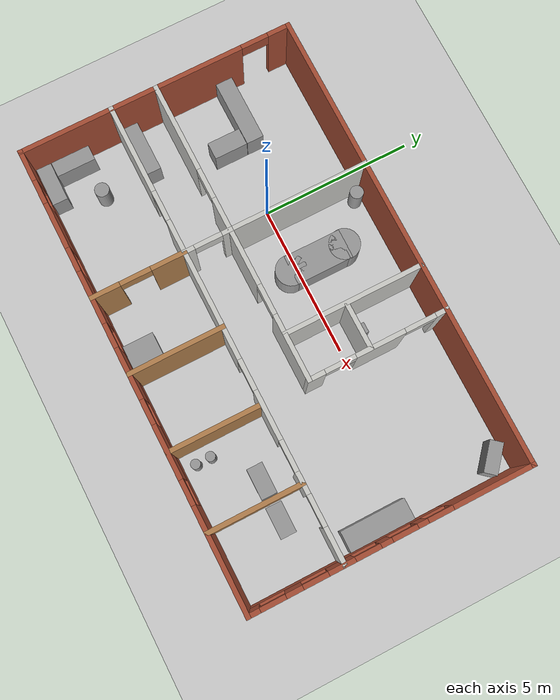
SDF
<sdf version="1.6">
 <world name="default">
  <light name="sun" type="directional">
   <pose>0 0 10 0 -0 0</pose>
   <diffuse>0.8 0.8 0.8 1</diffuse>
   <specular>0.2 0.2 0.2 1</specular>
   <attenuation>
    <range>1000</range>
    <constant>0.9</constant>
    <linear>0.01</linear>
    <quadratic>0.001</quadratic>
   </attenuation>
   <direction>-0.5 0.1 -0.9</direction>
  </light>
  <model name="ground_plane">
   <static>1</static>
   <link name="link">
    <collision name="collision">
     <geometry><plane><normal>0 0 1</normal><size>100 100</size></plane></geometry>
     <surface><friction><ode><mu>100</mu><mu2>50</mu2></ode></friction></surface>
    </collision>
    <visual name="visual">
     <cast_shadows>0</cast_shadows>
     <geometry><plane><normal>0 0 1</normal><size>100 100</size></plane></geometry>
     <material>
      <script><uri>file://media/materials/scripts/gazebo.material</uri><name>Gazebo/Grey</name></script>
     </material>
    </visual>
   </link>
  </model>
  <gravity>0 0 -9.8</gravity>
  <magnetic_field>6e-06 2.3e-05 -4.2e-05</magnetic_field>
  <atmosphere type="adiabatic"/>
  <physics name="default_physics" default="0" type="ode">
   <max_step_size>0.001</max_step_size>
   <real_time_factor>1</real_time_factor>
   <real_time_update_rate>1000</real_time_update_rate>
  </physics>
  <scene><ambient>0.4 0.4 0.4 1</ambient><background>0.7 0.7 0.7 1</background><shadows>1</shadows></scene>
  <spherical_coordinates>
   <surface_model>EARTH_WGS84</surface_model>
   <latitude_deg>0</latitude_deg>
   <longitude_deg>0</longitude_deg>
   <elevation>0</elevation>
   <heading_deg>0</heading_deg>
  </spherical_coordinates>
  <model name="building">
   <link name="Wall_0">
    <pose>0 4.5 0 0 -0 0</pose>
    <visual name="Wall_0_Visual">
     <pose>0 0 1.25 0 -0 0</pose>
     <geometry><box><size>15.15 0.15 2.5</size></box></geometry>
     <material>
      <script><uri>file://media/materials/scripts/gazebo.material</uri><name>Gazebo/Bricks</name></script>
      <ambient>0.996078 0.47451 0.0196078 1</ambient>
      <shader type="pixel"/>
      <diffuse>1 1 1 1</diffuse>
      <specular>0.2 0.2 0.2 1</specular>
      <emissive>0 0 0 1</emissive>
     </material>
     <meta><layer>0</layer></meta>
    </visual>
    <collision name="Wall_0_Collision">
     <pose>0 0 1.25 0 -0 0</pose>
     <geometry><box><size>15.15 0.15 2.5</size></box></geometry>
     <surface>
      <friction>
       <ode><mu>1</mu><mu2>1</mu2><fdir1>0 0 0</fdir1><slip1>0</slip1><slip2>0</slip2></ode>
       <torsional>
        <coefficient>1</coefficient>
        <patch_radius>0</patch_radius>
        <surface_radius>0</surface_radius>
        <use_patch_radius>1</use_patch_radius>
        <ode><slip>0</slip></ode>
       </torsional>
      </friction>
      <bounce><restitution_coefficient>0</restitution_coefficient><threshold>1e+06</threshold></bounce>
      <contact>
       <collide_without_contact>0</collide_without_contact>
       <collide_without_contact_bitmask>1</collide_without_contact_bitmask>
       <collide_bitmask>1</collide_bitmask>
       <ode>
        <soft_cfm>0</soft_cfm>
        <soft_erp>0.2</soft_erp>
        <kp>1e+13</kp>
        <kd>1</kd>
        <max_vel>0.01</max_vel>
        <min_depth>0</min_depth>
       </ode>
       <bullet>
        <split_impulse>1</split_impulse>
        <split_impulse_penetration_threshold>-0.01</split_impulse_penetration_threshold>
        <soft_cfm>0</soft_cfm>
        <soft_erp>0.2</soft_erp>
        <kp>1e+13</kp>
        <kd>1</kd>
       </bullet>
      </contact>
     </surface>
    </collision>
   </link>
   <link name="Wall_11">
    <pose>5 -3 0 0 0 -1.5708</pose>
    <visual name="Wall_11_Visual">
     <pose>0 0 1.25 0 -0 0</pose>
     <geometry><box><size>3.15 0.15 2.5</size></box></geometry>
     <material>
      <script><uri>file://media/materials/scripts/gazebo.material</uri><name>Gazebo/Wood</name></script>
      <ambient>0.435294 0.796078 0.67451 1</ambient>
      <shader type="pixel"/>
      <diffuse>1 1 1 1</diffuse>
      <specular>0.2 0.2 0.2 1</specular>
      <emissive>0 0 0 1</emissive>
     </material>
     <meta><layer>0</layer></meta>
    </visual>
    <collision name="Wall_11_Collision">
     <pose>0 0 1.25 0 -0 0</pose>
     <geometry><box><size>3.15 0.15 2.5</size></box></geometry>
     <surface>
      <friction>
       <ode><mu>1</mu><mu2>1</mu2><fdir1>0 0 0</fdir1><slip1>0</slip1><slip2>0</slip2></ode>
       <torsional>
        <coefficient>1</coefficient>
        <patch_radius>0</patch_radius>
        <surface_radius>0</surface_radius>
        <use_patch_radius>1</use_patch_radius>
        <ode><slip>0</slip></ode>
       </torsional>
      </friction>
      <bounce><restitution_coefficient>0</restitution_coefficient><threshold>1e+06</threshold></bounce>
      <contact>
       <collide_without_contact>0</collide_without_contact>
       <collide_without_contact_bitmask>1</collide_without_contact_bitmask>
       <collide_bitmask>1</collide_bitmask>
       <ode>
        <soft_cfm>0</soft_cfm>
        <soft_erp>0.2</soft_erp>
        <kp>1e+13</kp>
        <kd>1</kd>
        <max_vel>0.01</max_vel>
        <min_depth>0</min_depth>
       </ode>
       <bullet>
        <split_impulse>1</split_impulse>
        <split_impulse_penetration_threshold>-0.01</split_impulse_penetration_threshold>
        <soft_cfm>0</soft_cfm>
        <soft_erp>0.2</soft_erp>
        <kp>1e+13</kp>
        <kd>1</kd>
       </bullet>
      </contact>
     </surface>
    </collision>
   </link>
   <link name="Wall_13">
    <pose>2.5 -3 0 0 0 -1.5708</pose>
    <visual name="Wall_13_Visual">
     <pose>0 0 1.25 0 -0 0</pose>
     <geometry><box><size>3.15 0.15 2.5</size></box></geometry>
     <material>
      <script><uri>file://media/materials/scripts/gazebo.material</uri><name>Gazebo/Wood</name></script>
      <ambient>0.435294 0.796078 0.67451 1</ambient>
      <shader type="pixel"/>
      <diffuse>1 1 1 1</diffuse>
      <specular>0.2 0.2 0.2 1</specular>
      <emissive>0 0 0 1</emissive>
     </material>
     <meta><layer>0</layer></meta>
    </visual>
    <collision name="Wall_13_Collision">
     <pose>0 0 1.25 0 -0 0</pose>
     <geometry><box><size>3.15 0.15 2.5</size></box></geometry>
     <surface>
      <friction>
       <ode><mu>1</mu><mu2>1</mu2><fdir1>0 0 0</fdir1><slip1>0</slip1><slip2>0</slip2></ode>
       <torsional>
        <coefficient>1</coefficient>
        <patch_radius>0</patch_radius>
        <surface_radius>0</surface_radius>
        <use_patch_radius>1</use_patch_radius>
        <ode><slip>0</slip></ode>
       </torsional>
      </friction>
      <bounce><restitution_coefficient>0</restitution_coefficient><threshold>1e+06</threshold></bounce>
      <contact>
       <collide_without_contact>0</collide_without_contact>
       <collide_without_contact_bitmask>1</collide_without_contact_bitmask>
       <collide_bitmask>1</collide_bitmask>
       <ode>
        <soft_cfm>0</soft_cfm>
        <soft_erp>0.2</soft_erp>
        <kp>1e+13</kp>
        <kd>1</kd>
        <max_vel>0.01</max_vel>
        <min_depth>0</min_depth>
       </ode>
       <bullet>
        <split_impulse>1</split_impulse>
        <split_impulse_penetration_threshold>-0.01</split_impulse_penetration_threshold>
        <soft_cfm>0</soft_cfm>
        <soft_erp>0.2</soft_erp>
        <kp>1e+13</kp>
        <kd>1</kd>
       </bullet>
      </contact>
     </surface>
    </collision>
   </link>
   <link name="Wall_15">
    <pose>0 -3 0 0 0 -1.5708</pose>
    <visual name="Wall_15_Visual">
     <pose>0 0 1.25 0 -0 0</pose>
     <geometry><box><size>3.15 0.15 2.5</size></box></geometry>
     <material>
      <script><uri>file://media/materials/scripts/gazebo.material</uri><name>Gazebo/Wood</name></script>
      <ambient>0.435294 0.796078 0.67451 1</ambient>
      <shader type="pixel"/>
      <diffuse>1 1 1 1</diffuse>
      <specular>0.2 0.2 0.2 1</specular>
      <emissive>0 0 0 1</emissive>
     </material>
     <meta><layer>0</layer></meta>
    </visual>
    <collision name="Wall_15_Collision">
     <pose>0 0 1.25 0 -0 0</pose>
     <geometry><box><size>3.15 0.15 2.5</size></box></geometry>
     <surface>
      <friction>
       <ode><mu>1</mu><mu2>1</mu2><fdir1>0 0 0</fdir1><slip1>0</slip1><slip2>0</slip2></ode>
       <torsional>
        <coefficient>1</coefficient>
        <patch_radius>0</patch_radius>
        <surface_radius>0</surface_radius>
        <use_patch_radius>1</use_patch_radius>
        <ode><slip>0</slip></ode>
       </torsional>
      </friction>
      <bounce><restitution_coefficient>0</restitution_coefficient><threshold>1e+06</threshold></bounce>
      <contact>
       <collide_without_contact>0</collide_without_contact>
       <collide_without_contact_bitmask>1</collide_without_contact_bitmask>
       <collide_bitmask>1</collide_bitmask>
       <ode>
        <soft_cfm>0</soft_cfm>
        <soft_erp>0.2</soft_erp>
        <kp>1e+13</kp>
        <kd>1</kd>
        <max_vel>0.01</max_vel>
        <min_depth>0</min_depth>
       </ode>
       <bullet>
        <split_impulse>1</split_impulse>
        <split_impulse_penetration_threshold>-0.01</split_impulse_penetration_threshold>
        <soft_cfm>0</soft_cfm>
        <soft_erp>0.2</soft_erp>
        <kp>1e+13</kp>
        <kd>1</kd>
       </bullet>
      </contact>
     </surface>
    </collision>
   </link>
   <link name="Wall_17">
    <pose>-2.5 -3 0 0 0 -1.5708</pose>
    <visual name="Wall_17_Visual_0">
     <pose>-0.986122 0 1.25 0 -0 0</pose>
     <geometry><box><size>1.17776 0.15 2.5</size></box></geometry>
     <material>
      <script><uri>file://media/materials/scripts/gazebo.material</uri><name>Gazebo/Wood</name></script>
      <ambient>0.435294 0.796078 0.67451 1</ambient>
      <shader type="pixel"/>
      <diffuse>1 1 1 1</diffuse>
      <specular>0.2 0.2 0.2 1</specular>
      <emissive>0 0 0 1</emissive>
     </material>
     <meta><layer>0</layer></meta>
    </visual>
    <visual name="Wall_17_Visual_2">
     <pose>0.102756 0 2.25 0 -0 0</pose>
     <geometry><box><size>1 0.15 0.5</size></box></geometry>
     <material>
      <script><uri>file://media/materials/scripts/gazebo.material</uri><name>Gazebo/Wood</name></script>
      <ambient>0.435294 0.796078 0.67451 1</ambient>
      <shader type="pixel"/>
      <diffuse>1 1 1 1</diffuse>
      <specular>0.2 0.2 0.2 1</specular>
      <emissive>0 0 0 1</emissive>
     </material>
     <meta><layer>0</layer></meta>
    </visual>
    <visual name="Wall_17_Visual_1">
     <pose>1.08888 0 1.25 0 -0 0</pose>
     <geometry><box><size>0.972244 0.15 2.5</size></box></geometry>
     <material>
      <script><uri>file://media/materials/scripts/gazebo.material</uri><name>Gazebo/Wood</name></script>
      <ambient>0.435294 0.796078 0.67451 1</ambient>
      <shader type="pixel"/>
      <diffuse>1 1 1 1</diffuse>
      <specular>0.2 0.2 0.2 1</specular>
      <emissive>0 0 0 1</emissive>
     </material>
     <meta><layer>0</layer></meta>
    </visual>
    <collision name="Wall_17_Collision_2">
     <pose>0.102756 0 2.25 0 -0 0</pose>
     <geometry><box><size>1 0.15 0.5</size></box></geometry>
     <surface>
      <friction>
       <ode><mu>1</mu><mu2>1</mu2><fdir1>0 0 0</fdir1><slip1>0</slip1><slip2>0</slip2></ode>
       <torsional>
        <coefficient>1</coefficient>
        <patch_radius>0</patch_radius>
        <surface_radius>0</surface_radius>
        <use_patch_radius>1</use_patch_radius>
        <ode><slip>0</slip></ode>
       </torsional>
      </friction>
      <bounce><restitution_coefficient>0</restitution_coefficient><threshold>1e+06</threshold></bounce>
      <contact>
       <collide_without_contact>0</collide_without_contact>
       <collide_without_contact_bitmask>1</collide_without_contact_bitmask>
       <collide_bitmask>1</collide_bitmask>
       <ode>
        <soft_cfm>0</soft_cfm>
        <soft_erp>0.2</soft_erp>
        <kp>1e+13</kp>
        <kd>1</kd>
        <max_vel>0.01</max_vel>
        <min_depth>0</min_depth>
       </ode>
       <bullet>
        <split_impulse>1</split_impulse>
        <split_impulse_penetration_threshold>-0.01</split_impulse_penetration_threshold>
        <soft_cfm>0</soft_cfm>
        <soft_erp>0.2</soft_erp>
        <kp>1e+13</kp>
        <kd>1</kd>
       </bullet>
      </contact>
     </surface>
    </collision>
    <collision name="Wall_17_Collision_0">
     <pose>-0.986122 0 1.25 0 -0 0</pose>
     <geometry><box><size>1.17776 0.15 2.5</size></box></geometry>
     <surface>
      <friction>
       <ode><mu>1</mu><mu2>1</mu2><fdir1>0 0 0</fdir1><slip1>0</slip1><slip2>0</slip2></ode>
       <torsional>
        <coefficient>1</coefficient>
        <patch_radius>0</patch_radius>
        <surface_radius>0</surface_radius>
        <use_patch_radius>1</use_patch_radius>
        <ode><slip>0</slip></ode>
       </torsional>
      </friction>
      <bounce><restitution_coefficient>0</restitution_coefficient><threshold>1e+06</threshold></bounce>
      <contact>
       <collide_without_contact>0</collide_without_contact>
       <collide_without_contact_bitmask>1</collide_without_contact_bitmask>
       <collide_bitmask>1</collide_bitmask>
       <ode>
        <soft_cfm>0</soft_cfm>
        <soft_erp>0.2</soft_erp>
        <kp>1e+13</kp>
        <kd>1</kd>
        <max_vel>0.01</max_vel>
        <min_depth>0</min_depth>
       </ode>
       <bullet>
        <split_impulse>1</split_impulse>
        <split_impulse_penetration_threshold>-0.01</split_impulse_penetration_threshold>
        <soft_cfm>0</soft_cfm>
        <soft_erp>0.2</soft_erp>
        <kp>1e+13</kp>
        <kd>1</kd>
       </bullet>
      </contact>
     </surface>
    </collision>
    <collision name="Wall_17_Collision_1">
     <pose>1.08888 0 1.25 0 -0 0</pose>
     <geometry><box><size>0.972244 0.15 2.5</size></box></geometry>
     <surface>
      <friction>
       <ode><mu>1</mu><mu2>1</mu2><fdir1>0 0 0</fdir1><slip1>0</slip1><slip2>0</slip2></ode>
       <torsional>
        <coefficient>1</coefficient>
        <patch_radius>0</patch_radius>
        <surface_radius>0</surface_radius>
        <use_patch_radius>1</use_patch_radius>
        <ode><slip>0</slip></ode>
       </torsional>
      </friction>
      <bounce><restitution_coefficient>0</restitution_coefficient><threshold>1e+06</threshold></bounce>
      <contact>
       <collide_without_contact>0</collide_without_contact>
       <collide_without_contact_bitmask>1</collide_without_contact_bitmask>
       <collide_bitmask>1</collide_bitmask>
       <ode>
        <soft_cfm>0</soft_cfm>
        <soft_erp>0.2</soft_erp>
        <kp>1e+13</kp>
        <kd>1</kd>
        <max_vel>0.01</max_vel>
        <min_depth>0</min_depth>
       </ode>
       <bullet>
        <split_impulse>1</split_impulse>
        <split_impulse_penetration_threshold>-0.01</split_impulse_penetration_threshold>
        <soft_cfm>0</soft_cfm>
        <soft_erp>0.2</soft_erp>
        <kp>1e+13</kp>
        <kd>1</kd>
       </bullet>
      </contact>
     </surface>
    </collision>
   </link>
   <link name="Wall_19">
    <pose>-2.5 0 0 0 -0 0</pose>
    <visual name="Wall_19_Visual_1">
     <pose>0.383063 0 1.25 0 -0 0</pose>
     <geometry><box><size>2.95551 0.15 2.5</size></box></geometry>
     <material>
      <script><uri>file://media/materials/scripts/gazebo.material</uri><name>Gazebo/CeilingTiled</name></script>
      <ambient>1 0.764706 0.305882 1</ambient>
      <shader type="pixel"/>
      <diffuse>1 1 1 1</diffuse>
      <specular>0 0 0 1</specular>
      <emissive>0 0 0 1</emissive>
     </material>
     <meta><layer>0</layer></meta>
    </visual>
    <visual name="Wall_19_Visual_2">
     <pose>3.96791 0 1.25 0 -0 0</pose>
     <geometry><box><size>2.21418 0.15 2.5</size></box></geometry>
     <material>
      <script><uri>file://media/materials/scripts/gazebo.material</uri><name>Gazebo/CeilingTiled</name></script>
      <ambient>1 0.764706 0.305882 1</ambient>
      <shader type="pixel"/>
      <diffuse>1 1 1 1</diffuse>
      <specular>0 0 0 1</specular>
      <emissive>0 0 0 1</emissive>
     </material>
     <meta><layer>0</layer></meta>
    </visual>
    <visual name="Wall_19_Visual_0">
     <pose>-3.58485 0 1.25 0 -0 0</pose>
     <geometry><box><size>2.98031 0.15 2.5</size></box></geometry>
     <material>
      <script><uri>file://media/materials/scripts/gazebo.material</uri><name>Gazebo/CeilingTiled</name></script>
      <ambient>1 0.764706 0.305882 1</ambient>
      <shader type="pixel"/>
      <diffuse>1 1 1 1</diffuse>
      <specular>0 0 0 1</specular>
      <emissive>0 0 0 1</emissive>
     </material>
     <meta><layer>0</layer></meta>
    </visual>
    <visual name="Wall_19_Visual_4">
     <pose>2.36082 0 2.25 0 -0 0</pose>
     <geometry><box><size>1 0.15 0.5</size></box></geometry>
     <material>
      <script><uri>file://media/materials/scripts/gazebo.material</uri><name>Gazebo/CeilingTiled</name></script>
      <ambient>1 0.764706 0.305882 1</ambient>
      <shader type="pixel"/>
      <diffuse>1 1 1 1</diffuse>
      <specular>0 0 0 1</specular>
      <emissive>0 0 0 1</emissive>
     </material>
     <meta><layer>0</layer></meta>
    </visual>
    <visual name="Wall_19_Visual_3">
     <pose>-1.59469 0 2.25 0 -0 0</pose>
     <geometry><box><size>1 0.15 0.5</size></box></geometry>
     <material>
      <script><uri>file://media/materials/scripts/gazebo.material</uri><name>Gazebo/CeilingTiled</name></script>
      <ambient>1 0.764706 0.305882 1</ambient>
      <shader type="pixel"/>
      <diffuse>1 1 1 1</diffuse>
      <specular>0 0 0 1</specular>
      <emissive>0 0 0 1</emissive>
     </material>
     <meta><layer>0</layer></meta>
    </visual>
    <collision name="Wall_19_Collision_0">
     <pose>-3.58485 0 1.25 0 -0 0</pose>
     <geometry><box><size>2.98031 0.15 2.5</size></box></geometry>
     <surface>
      <friction>
       <ode><mu>1</mu><mu2>1</mu2><fdir1>0 0 0</fdir1><slip1>0</slip1><slip2>0</slip2></ode>
       <torsional>
        <coefficient>1</coefficient>
        <patch_radius>0</patch_radius>
        <surface_radius>0</surface_radius>
        <use_patch_radius>1</use_patch_radius>
        <ode><slip>0</slip></ode>
       </torsional>
      </friction>
      <bounce><restitution_coefficient>0</restitution_coefficient><threshold>1e+06</threshold></bounce>
      <contact>
       <collide_without_contact>0</collide_without_contact>
       <collide_without_contact_bitmask>1</collide_without_contact_bitmask>
       <collide_bitmask>1</collide_bitmask>
       <ode>
        <soft_cfm>0</soft_cfm>
        <soft_erp>0.2</soft_erp>
        <kp>1e+13</kp>
        <kd>1</kd>
        <max_vel>0.01</max_vel>
        <min_depth>0</min_depth>
       </ode>
       <bullet>
        <split_impulse>1</split_impulse>
        <split_impulse_penetration_threshold>-0.01</split_impulse_penetration_threshold>
        <soft_cfm>0</soft_cfm>
        <soft_erp>0.2</soft_erp>
        <kp>1e+13</kp>
        <kd>1</kd>
       </bullet>
      </contact>
     </surface>
    </collision>
    <collision name="Wall_19_Collision_2">
     <pose>3.96791 0 1.25 0 -0 0</pose>
     <geometry><box><size>2.21418 0.15 2.5</size></box></geometry>
     <surface>
      <friction>
       <ode><mu>1</mu><mu2>1</mu2><fdir1>0 0 0</fdir1><slip1>0</slip1><slip2>0</slip2></ode>
       <torsional>
        <coefficient>1</coefficient>
        <patch_radius>0</patch_radius>
        <surface_radius>0</surface_radius>
        <use_patch_radius>1</use_patch_radius>
        <ode><slip>0</slip></ode>
       </torsional>
      </friction>
      <bounce><restitution_coefficient>0</restitution_coefficient><threshold>1e+06</threshold></bounce>
      <contact>
       <collide_without_contact>0</collide_without_contact>
       <collide_without_contact_bitmask>1</collide_without_contact_bitmask>
       <collide_bitmask>1</collide_bitmask>
       <ode>
        <soft_cfm>0</soft_cfm>
        <soft_erp>0.2</soft_erp>
        <kp>1e+13</kp>
        <kd>1</kd>
        <max_vel>0.01</max_vel>
        <min_depth>0</min_depth>
       </ode>
       <bullet>
        <split_impulse>1</split_impulse>
        <split_impulse_penetration_threshold>-0.01</split_impulse_penetration_threshold>
        <soft_cfm>0</soft_cfm>
        <soft_erp>0.2</soft_erp>
        <kp>1e+13</kp>
        <kd>1</kd>
       </bullet>
      </contact>
     </surface>
    </collision>
    <collision name="Wall_19_Collision_1">
     <pose>0.383063 0 1.25 0 -0 0</pose>
     <geometry><box><size>2.95551 0.15 2.5</size></box></geometry>
     <surface>
      <friction>
       <ode><mu>1</mu><mu2>1</mu2><fdir1>0 0 0</fdir1><slip1>0</slip1><slip2>0</slip2></ode>
       <torsional>
        <coefficient>1</coefficient>
        <patch_radius>0</patch_radius>
        <surface_radius>0</surface_radius>
        <use_patch_radius>1</use_patch_radius>
        <ode><slip>0</slip></ode>
       </torsional>
      </friction>
      <bounce><restitution_coefficient>0</restitution_coefficient><threshold>1e+06</threshold></bounce>
      <contact>
       <collide_without_contact>0</collide_without_contact>
       <collide_without_contact_bitmask>1</collide_without_contact_bitmask>
       <collide_bitmask>1</collide_bitmask>
       <ode>
        <soft_cfm>0</soft_cfm>
        <soft_erp>0.2</soft_erp>
        <kp>1e+13</kp>
        <kd>1</kd>
        <max_vel>0.01</max_vel>
        <min_depth>0</min_depth>
       </ode>
       <bullet>
        <split_impulse>1</split_impulse>
        <split_impulse_penetration_threshold>-0.01</split_impulse_penetration_threshold>
        <soft_cfm>0</soft_cfm>
        <soft_erp>0.2</soft_erp>
        <kp>1e+13</kp>
        <kd>1</kd>
       </bullet>
      </contact>
     </surface>
    </collision>
    <collision name="Wall_19_Collision_3">
     <pose>-1.59469 0 2.25 0 -0 0</pose>
     <geometry><box><size>1 0.15 0.5</size></box></geometry>
     <surface>
      <friction>
       <ode><mu>1</mu><mu2>1</mu2><fdir1>0 0 0</fdir1><slip1>0</slip1><slip2>0</slip2></ode>
       <torsional>
        <coefficient>1</coefficient>
        <patch_radius>0</patch_radius>
        <surface_radius>0</surface_radius>
        <use_patch_radius>1</use_patch_radius>
        <ode><slip>0</slip></ode>
       </torsional>
      </friction>
      <bounce><restitution_coefficient>0</restitution_coefficient><threshold>1e+06</threshold></bounce>
      <contact>
       <collide_without_contact>0</collide_without_contact>
       <collide_without_contact_bitmask>1</collide_without_contact_bitmask>
       <collide_bitmask>1</collide_bitmask>
       <ode>
        <soft_cfm>0</soft_cfm>
        <soft_erp>0.2</soft_erp>
        <kp>1e+13</kp>
        <kd>1</kd>
        <max_vel>0.01</max_vel>
        <min_depth>0</min_depth>
       </ode>
       <bullet>
        <split_impulse>1</split_impulse>
        <split_impulse_penetration_threshold>-0.01</split_impulse_penetration_threshold>
        <soft_cfm>0</soft_cfm>
        <soft_erp>0.2</soft_erp>
        <kp>1e+13</kp>
        <kd>1</kd>
       </bullet>
      </contact>
     </surface>
    </collision>
    <collision name="Wall_19_Collision_4">
     <pose>2.36082 0 2.25 0 -0 0</pose>
     <geometry><box><size>1 0.15 0.5</size></box></geometry>
     <surface>
      <friction>
       <ode><mu>1</mu><mu2>1</mu2><fdir1>0 0 0</fdir1><slip1>0</slip1><slip2>0</slip2></ode>
       <torsional>
        <coefficient>1</coefficient>
        <patch_radius>0</patch_radius>
        <surface_radius>0</surface_radius>
        <use_patch_radius>1</use_patch_radius>
        <ode><slip>0</slip></ode>
       </torsional>
      </friction>
      <bounce><restitution_coefficient>0</restitution_coefficient><threshold>1e+06</threshold></bounce>
      <contact>
       <collide_without_contact>0</collide_without_contact>
       <collide_without_contact_bitmask>1</collide_without_contact_bitmask>
       <collide_bitmask>1</collide_bitmask>
       <ode>
        <soft_cfm>0</soft_cfm>
        <soft_erp>0.2</soft_erp>
        <kp>1e+13</kp>
        <kd>1</kd>
        <max_vel>0.01</max_vel>
        <min_depth>0</min_depth>
       </ode>
       <bullet>
        <split_impulse>1</split_impulse>
        <split_impulse_penetration_threshold>-0.01</split_impulse_penetration_threshold>
        <soft_cfm>0</soft_cfm>
        <soft_erp>0.2</soft_erp>
        <kp>1e+13</kp>
        <kd>1</kd>
       </bullet>
      </contact>
     </surface>
    </collision>
   </link>
   <link name="Wall_2">
    <pose>7.5 0 0 0 0 -1.5708</pose>
    <visual name="Wall_2_Visual_1">
     <pose>1.32605 0 0.5 0 -0 0</pose>
     <geometry><box><size>6.4979 0.15 1</size></box></geometry>
     <material>
      <script><uri>file://media/materials/scripts/gazebo.material</uri><name>Gazebo/Bricks</name></script>
      <ambient>0.996078 0.47451 0.0196078 1</ambient>
      <shader type="pixel"/>
      <diffuse>1 1 1 1</diffuse>
      <specular>0.2 0.2 0.2 1</specular>
      <emissive>0 0 0 1</emissive>
     </material>
     <meta><layer>0</layer></meta>
    </visual>
    <visual name="Wall_2_Visual_6">
     <pose>4.34943 0 1.75 0 -0 0</pose>
     <geometry><box><size>0.451131 0.15 1.5</size></box></geometry>
     <material>
      <script><uri>file://media/materials/scripts/gazebo.material</uri><name>Gazebo/Bricks</name></script>
      <ambient>0.996078 0.47451 0.0196078 1</ambient>
      <shader type="pixel"/>
      <diffuse>1 1 1 1</diffuse>
      <specular>0.2 0.2 0.2 1</specular>
      <emissive>0 0 0 1</emissive>
     </material>
     <meta><layer>0</layer></meta>
    </visual>
    <visual name="Wall_2_Visual_9">
     <pose>0.765409 0 2.35 0 -0 0</pose>
     <geometry><box><size>0.8 0.15 0.3</size></box></geometry>
     <material>
      <script><uri>file://media/materials/scripts/gazebo.material</uri><name>Gazebo/Bricks</name></script>
      <ambient>0.996078 0.47451 0.0196078 1</ambient>
      <shader type="pixel"/>
      <diffuse>1 1 1 1</diffuse>
      <specular>0.2 0.2 0.2 1</specular>
      <emissive>0 0 0 1</emissive>
     </material>
     <meta><layer>0</layer></meta>
    </visual>
    <visual name="Wall_2_Visual_8">
     <pose>-0.395093 0 2.35 0 -0 0</pose>
     <geometry><box><size>0.8 0.15 0.3</size></box></geometry>
     <material>
      <script><uri>file://media/materials/scripts/gazebo.material</uri><name>Gazebo/Bricks</name></script>
      <ambient>0.996078 0.47451 0.0196078 1</ambient>
      <shader type="pixel"/>
      <diffuse>1 1 1 1</diffuse>
      <specular>0.2 0.2 0.2 1</specular>
      <emissive>0 0 0 1</emissive>
     </material>
     <meta><layer>0</layer></meta>
    </visual>
    <visual name="Wall_2_Visual_10">
     <pose>2.39992 0 2.35 0 -0 0</pose>
     <geometry><box><size>0.8 0.15 0.3</size></box></geometry>
     <material>
      <script><uri>file://media/materials/scripts/gazebo.material</uri><name>Gazebo/Bricks</name></script>
      <ambient>0.996078 0.47451 0.0196078 1</ambient>
      <shader type="pixel"/>
      <diffuse>1 1 1 1</diffuse>
      <specular>0.2 0.2 0.2 1</specular>
      <emissive>0 0 0 1</emissive>
     </material>
     <meta><layer>0</layer></meta>
    </visual>
    <visual name="Wall_2_Visual_5">
     <pose>3.06189 0 1.75 0 -0 0</pose>
     <geometry><box><size>0.523952 0.15 1.5</size></box></geometry>
     <material>
      <script><uri>file://media/materials/scripts/gazebo.material</uri><name>Gazebo/Bricks</name></script>
      <ambient>0.996078 0.47451 0.0196078 1</ambient>
      <shader type="pixel"/>
      <diffuse>1 1 1 1</diffuse>
      <specular>0.2 0.2 0.2 1</specular>
      <emissive>0 0 0 1</emissive>
     </material>
     <meta><layer>0</layer></meta>
    </visual>
    <visual name="Wall_2_Visual_4">
     <pose>1.58266 0 1.75 0 -0 0</pose>
     <geometry><box><size>0.834509 0.15 1.5</size></box></geometry>
     <material>
      <script><uri>file://media/materials/scripts/gazebo.material</uri><name>Gazebo/Bricks</name></script>
      <ambient>0.996078 0.47451 0.0196078 1</ambient>
      <shader type="pixel"/>
      <diffuse>1 1 1 1</diffuse>
      <specular>0.2 0.2 0.2 1</specular>
      <emissive>0 0 0 1</emissive>
     </material>
     <meta><layer>0</layer></meta>
    </visual>
    <visual name="Wall_2_Visual_7">
     <pose>-1.5229 0 2.35 0 -0 0</pose>
     <geometry><box><size>0.8 0.15 0.3</size></box></geometry>
     <material>
      <script><uri>file://media/materials/scripts/gazebo.material</uri><name>Gazebo/Bricks</name></script>
      <ambient>0.996078 0.47451 0.0196078 1</ambient>
      <shader type="pixel"/>
      <diffuse>1 1 1 1</diffuse>
      <specular>0.2 0.2 0.2 1</specular>
      <emissive>0 0 0 1</emissive>
     </material>
     <meta><layer>0</layer></meta>
    </visual>
    <visual name="Wall_2_Visual_0">
     <pose>-3.24895 0 1.25 0 -0 0</pose>
     <geometry><box><size>2.6521 0.15 2.5</size></box></geometry>
     <material>
      <script><uri>file://media/materials/scripts/gazebo.material</uri><name>Gazebo/Bricks</name></script>
      <ambient>0.996078 0.47451 0.0196078 1</ambient>
      <shader type="pixel"/>
      <diffuse>1 1 1 1</diffuse>
      <specular>0.2 0.2 0.2 1</specular>
      <emissive>0 0 0 1</emissive>
     </material>
     <meta><layer>0</layer></meta>
    </visual>
    <visual name="Wall_2_Visual_3">
     <pose>0.185158 0 1.75 0 -0 0</pose>
     <geometry><box><size>0.360501 0.15 1.5</size></box></geometry>
     <material>
      <script><uri>file://media/materials/scripts/gazebo.material</uri><name>Gazebo/Bricks</name></script>
      <ambient>0.996078 0.47451 0.0196078 1</ambient>
      <shader type="pixel"/>
      <diffuse>1 1 1 1</diffuse>
      <specular>0.2 0.2 0.2 1</specular>
      <emissive>0 0 0 1</emissive>
     </material>
     <meta><layer>0</layer></meta>
    </visual>
    <visual name="Wall_2_Visual_2">
     <pose>-0.958999 0 1.75 0 -0 0</pose>
     <geometry><box><size>0.327811 0.15 1.5</size></box></geometry>
     <material>
      <script><uri>file://media/materials/scripts/gazebo.material</uri><name>Gazebo/Bricks</name></script>
      <ambient>0.996078 0.47451 0.0196078 1</ambient>
      <shader type="pixel"/>
      <diffuse>1 1 1 1</diffuse>
      <specular>0.2 0.2 0.2 1</specular>
      <emissive>0 0 0 1</emissive>
     </material>
     <meta><layer>0</layer></meta>
    </visual>
    <visual name="Wall_2_Visual_11">
     <pose>3.72387 0 2.35 0 -0 0</pose>
     <geometry><box><size>0.8 0.15 0.3</size></box></geometry>
     <material>
      <script><uri>file://media/materials/scripts/gazebo.material</uri><name>Gazebo/Bricks</name></script>
      <ambient>0.996078 0.47451 0.0196078 1</ambient>
      <shader type="pixel"/>
      <diffuse>1 1 1 1</diffuse>
      <specular>0.2 0.2 0.2 1</specular>
      <emissive>0 0 0 1</emissive>
     </material>
     <meta><layer>0</layer></meta>
    </visual>
    <collision name="Wall_2_Collision_5">
     <pose>3.06189 0 1.75 0 -0 0</pose>
     <geometry><box><size>0.523952 0.15 1.5</size></box></geometry>
     <surface>
      <friction>
       <ode><mu>1</mu><mu2>1</mu2><fdir1>0 0 0</fdir1><slip1>0</slip1><slip2>0</slip2></ode>
       <torsional>
        <coefficient>1</coefficient>
        <patch_radius>0</patch_radius>
        <surface_radius>0</surface_radius>
        <use_patch_radius>1</use_patch_radius>
        <ode><slip>0</slip></ode>
       </torsional>
      </friction>
      <bounce><restitution_coefficient>0</restitution_coefficient><threshold>1e+06</threshold></bounce>
      <contact>
       <collide_without_contact>0</collide_without_contact>
       <collide_without_contact_bitmask>1</collide_without_contact_bitmask>
       <collide_bitmask>1</collide_bitmask>
       <ode>
        <soft_cfm>0</soft_cfm>
        <soft_erp>0.2</soft_erp>
        <kp>1e+13</kp>
        <kd>1</kd>
        <max_vel>0.01</max_vel>
        <min_depth>0</min_depth>
       </ode>
       <bullet>
        <split_impulse>1</split_impulse>
        <split_impulse_penetration_threshold>-0.01</split_impulse_penetration_threshold>
        <soft_cfm>0</soft_cfm>
        <soft_erp>0.2</soft_erp>
        <kp>1e+13</kp>
        <kd>1</kd>
       </bullet>
      </contact>
     </surface>
    </collision>
    <collision name="Wall_2_Collision_9">
     <pose>0.765409 0 2.35 0 -0 0</pose>
     <geometry><box><size>0.8 0.15 0.3</size></box></geometry>
     <surface>
      <friction>
       <ode><mu>1</mu><mu2>1</mu2><fdir1>0 0 0</fdir1><slip1>0</slip1><slip2>0</slip2></ode>
       <torsional>
        <coefficient>1</coefficient>
        <patch_radius>0</patch_radius>
        <surface_radius>0</surface_radius>
        <use_patch_radius>1</use_patch_radius>
        <ode><slip>0</slip></ode>
       </torsional>
      </friction>
      <bounce><restitution_coefficient>0</restitution_coefficient><threshold>1e+06</threshold></bounce>
      <contact>
       <collide_without_contact>0</collide_without_contact>
       <collide_without_contact_bitmask>1</collide_without_contact_bitmask>
       <collide_bitmask>1</collide_bitmask>
       <ode>
        <soft_cfm>0</soft_cfm>
        <soft_erp>0.2</soft_erp>
        <kp>1e+13</kp>
        <kd>1</kd>
        <max_vel>0.01</max_vel>
        <min_depth>0</min_depth>
       </ode>
       <bullet>
        <split_impulse>1</split_impulse>
        <split_impulse_penetration_threshold>-0.01</split_impulse_penetration_threshold>
        <soft_cfm>0</soft_cfm>
        <soft_erp>0.2</soft_erp>
        <kp>1e+13</kp>
        <kd>1</kd>
       </bullet>
      </contact>
     </surface>
    </collision>
    <collision name="Wall_2_Collision_8">
     <pose>-0.395093 0 2.35 0 -0 0</pose>
     <geometry><box><size>0.8 0.15 0.3</size></box></geometry>
     <surface>
      <friction>
       <ode><mu>1</mu><mu2>1</mu2><fdir1>0 0 0</fdir1><slip1>0</slip1><slip2>0</slip2></ode>
       <torsional>
        <coefficient>1</coefficient>
        <patch_radius>0</patch_radius>
        <surface_radius>0</surface_radius>
        <use_patch_radius>1</use_patch_radius>
        <ode><slip>0</slip></ode>
       </torsional>
      </friction>
      <bounce><restitution_coefficient>0</restitution_coefficient><threshold>1e+06</threshold></bounce>
      <contact>
       <collide_without_contact>0</collide_without_contact>
       <collide_without_contact_bitmask>1</collide_without_contact_bitmask>
       <collide_bitmask>1</collide_bitmask>
       <ode>
        <soft_cfm>0</soft_cfm>
        <soft_erp>0.2</soft_erp>
        <kp>1e+13</kp>
        <kd>1</kd>
        <max_vel>0.01</max_vel>
        <min_depth>0</min_depth>
       </ode>
       <bullet>
        <split_impulse>1</split_impulse>
        <split_impulse_penetration_threshold>-0.01</split_impulse_penetration_threshold>
        <soft_cfm>0</soft_cfm>
        <soft_erp>0.2</soft_erp>
        <kp>1e+13</kp>
        <kd>1</kd>
       </bullet>
      </contact>
     </surface>
    </collision>
    <collision name="Wall_2_Collision_0">
     <pose>-3.24895 0 1.25 0 -0 0</pose>
     <geometry><box><size>2.6521 0.15 2.5</size></box></geometry>
     <surface>
      <friction>
       <ode><mu>1</mu><mu2>1</mu2><fdir1>0 0 0</fdir1><slip1>0</slip1><slip2>0</slip2></ode>
       <torsional>
        <coefficient>1</coefficient>
        <patch_radius>0</patch_radius>
        <surface_radius>0</surface_radius>
        <use_patch_radius>1</use_patch_radius>
        <ode><slip>0</slip></ode>
       </torsional>
      </friction>
      <bounce><restitution_coefficient>0</restitution_coefficient><threshold>1e+06</threshold></bounce>
      <contact>
       <collide_without_contact>0</collide_without_contact>
       <collide_without_contact_bitmask>1</collide_without_contact_bitmask>
       <collide_bitmask>1</collide_bitmask>
       <ode>
        <soft_cfm>0</soft_cfm>
        <soft_erp>0.2</soft_erp>
        <kp>1e+13</kp>
        <kd>1</kd>
        <max_vel>0.01</max_vel>
        <min_depth>0</min_depth>
       </ode>
       <bullet>
        <split_impulse>1</split_impulse>
        <split_impulse_penetration_threshold>-0.01</split_impulse_penetration_threshold>
        <soft_cfm>0</soft_cfm>
        <soft_erp>0.2</soft_erp>
        <kp>1e+13</kp>
        <kd>1</kd>
       </bullet>
      </contact>
     </surface>
    </collision>
    <collision name="Wall_2_Collision_6">
     <pose>4.34943 0 1.75 0 -0 0</pose>
     <geometry><box><size>0.451131 0.15 1.5</size></box></geometry>
     <surface>
      <friction>
       <ode><mu>1</mu><mu2>1</mu2><fdir1>0 0 0</fdir1><slip1>0</slip1><slip2>0</slip2></ode>
       <torsional>
        <coefficient>1</coefficient>
        <patch_radius>0</patch_radius>
        <surface_radius>0</surface_radius>
        <use_patch_radius>1</use_patch_radius>
        <ode><slip>0</slip></ode>
       </torsional>
      </friction>
      <bounce><restitution_coefficient>0</restitution_coefficient><threshold>1e+06</threshold></bounce>
      <contact>
       <collide_without_contact>0</collide_without_contact>
       <collide_without_contact_bitmask>1</collide_without_contact_bitmask>
       <collide_bitmask>1</collide_bitmask>
       <ode>
        <soft_cfm>0</soft_cfm>
        <soft_erp>0.2</soft_erp>
        <kp>1e+13</kp>
        <kd>1</kd>
        <max_vel>0.01</max_vel>
        <min_depth>0</min_depth>
       </ode>
       <bullet>
        <split_impulse>1</split_impulse>
        <split_impulse_penetration_threshold>-0.01</split_impulse_penetration_threshold>
        <soft_cfm>0</soft_cfm>
        <soft_erp>0.2</soft_erp>
        <kp>1e+13</kp>
        <kd>1</kd>
       </bullet>
      </contact>
     </surface>
    </collision>
    <collision name="Wall_2_Collision_7">
     <pose>-1.5229 0 2.35 0 -0 0</pose>
     <geometry><box><size>0.8 0.15 0.3</size></box></geometry>
     <surface>
      <friction>
       <ode><mu>1</mu><mu2>1</mu2><fdir1>0 0 0</fdir1><slip1>0</slip1><slip2>0</slip2></ode>
       <torsional>
        <coefficient>1</coefficient>
        <patch_radius>0</patch_radius>
        <surface_radius>0</surface_radius>
        <use_patch_radius>1</use_patch_radius>
        <ode><slip>0</slip></ode>
       </torsional>
      </friction>
      <bounce><restitution_coefficient>0</restitution_coefficient><threshold>1e+06</threshold></bounce>
      <contact>
       <collide_without_contact>0</collide_without_contact>
       <collide_without_contact_bitmask>1</collide_without_contact_bitmask>
       <collide_bitmask>1</collide_bitmask>
       <ode>
        <soft_cfm>0</soft_cfm>
        <soft_erp>0.2</soft_erp>
        <kp>1e+13</kp>
        <kd>1</kd>
        <max_vel>0.01</max_vel>
        <min_depth>0</min_depth>
       </ode>
       <bullet>
        <split_impulse>1</split_impulse>
        <split_impulse_penetration_threshold>-0.01</split_impulse_penetration_threshold>
        <soft_cfm>0</soft_cfm>
        <soft_erp>0.2</soft_erp>
        <kp>1e+13</kp>
        <kd>1</kd>
       </bullet>
      </contact>
     </surface>
    </collision>
    <collision name="Wall_2_Collision_11">
     <pose>3.72387 0 2.35 0 -0 0</pose>
     <geometry><box><size>0.8 0.15 0.3</size></box></geometry>
     <surface>
      <friction>
       <ode><mu>1</mu><mu2>1</mu2><fdir1>0 0 0</fdir1><slip1>0</slip1><slip2>0</slip2></ode>
       <torsional>
        <coefficient>1</coefficient>
        <patch_radius>0</patch_radius>
        <surface_radius>0</surface_radius>
        <use_patch_radius>1</use_patch_radius>
        <ode><slip>0</slip></ode>
       </torsional>
      </friction>
      <bounce><restitution_coefficient>0</restitution_coefficient><threshold>1e+06</threshold></bounce>
      <contact>
       <collide_without_contact>0</collide_without_contact>
       <collide_without_contact_bitmask>1</collide_without_contact_bitmask>
       <collide_bitmask>1</collide_bitmask>
       <ode>
        <soft_cfm>0</soft_cfm>
        <soft_erp>0.2</soft_erp>
        <kp>1e+13</kp>
        <kd>1</kd>
        <max_vel>0.01</max_vel>
        <min_depth>0</min_depth>
       </ode>
       <bullet>
        <split_impulse>1</split_impulse>
        <split_impulse_penetration_threshold>-0.01</split_impulse_penetration_threshold>
        <soft_cfm>0</soft_cfm>
        <soft_erp>0.2</soft_erp>
        <kp>1e+13</kp>
        <kd>1</kd>
       </bullet>
      </contact>
     </surface>
    </collision>
    <collision name="Wall_2_Collision_4">
     <pose>1.58266 0 1.75 0 -0 0</pose>
     <geometry><box><size>0.834509 0.15 1.5</size></box></geometry>
     <surface>
      <friction>
       <ode><mu>1</mu><mu2>1</mu2><fdir1>0 0 0</fdir1><slip1>0</slip1><slip2>0</slip2></ode>
       <torsional>
        <coefficient>1</coefficient>
        <patch_radius>0</patch_radius>
        <surface_radius>0</surface_radius>
        <use_patch_radius>1</use_patch_radius>
        <ode><slip>0</slip></ode>
       </torsional>
      </friction>
      <bounce><restitution_coefficient>0</restitution_coefficient><threshold>1e+06</threshold></bounce>
      <contact>
       <collide_without_contact>0</collide_without_contact>
       <collide_without_contact_bitmask>1</collide_without_contact_bitmask>
       <collide_bitmask>1</collide_bitmask>
       <ode>
        <soft_cfm>0</soft_cfm>
        <soft_erp>0.2</soft_erp>
        <kp>1e+13</kp>
        <kd>1</kd>
        <max_vel>0.01</max_vel>
        <min_depth>0</min_depth>
       </ode>
       <bullet>
        <split_impulse>1</split_impulse>
        <split_impulse_penetration_threshold>-0.01</split_impulse_penetration_threshold>
        <soft_cfm>0</soft_cfm>
        <soft_erp>0.2</soft_erp>
        <kp>1e+13</kp>
        <kd>1</kd>
       </bullet>
      </contact>
     </surface>
    </collision>
    <collision name="Wall_2_Collision_10">
     <pose>2.39992 0 2.35 0 -0 0</pose>
     <geometry><box><size>0.8 0.15 0.3</size></box></geometry>
     <surface>
      <friction>
       <ode><mu>1</mu><mu2>1</mu2><fdir1>0 0 0</fdir1><slip1>0</slip1><slip2>0</slip2></ode>
       <torsional>
        <coefficient>1</coefficient>
        <patch_radius>0</patch_radius>
        <surface_radius>0</surface_radius>
        <use_patch_radius>1</use_patch_radius>
        <ode><slip>0</slip></ode>
       </torsional>
      </friction>
      <bounce><restitution_coefficient>0</restitution_coefficient><threshold>1e+06</threshold></bounce>
      <contact>
       <collide_without_contact>0</collide_without_contact>
       <collide_without_contact_bitmask>1</collide_without_contact_bitmask>
       <collide_bitmask>1</collide_bitmask>
       <ode>
        <soft_cfm>0</soft_cfm>
        <soft_erp>0.2</soft_erp>
        <kp>1e+13</kp>
        <kd>1</kd>
        <max_vel>0.01</max_vel>
        <min_depth>0</min_depth>
       </ode>
       <bullet>
        <split_impulse>1</split_impulse>
        <split_impulse_penetration_threshold>-0.01</split_impulse_penetration_threshold>
        <soft_cfm>0</soft_cfm>
        <soft_erp>0.2</soft_erp>
        <kp>1e+13</kp>
        <kd>1</kd>
       </bullet>
      </contact>
     </surface>
    </collision>
    <collision name="Wall_2_Collision_1">
     <pose>1.32605 0 0.5 0 -0 0</pose>
     <geometry><box><size>6.4979 0.15 1</size></box></geometry>
     <surface>
      <friction>
       <ode><mu>1</mu><mu2>1</mu2><fdir1>0 0 0</fdir1><slip1>0</slip1><slip2>0</slip2></ode>
       <torsional>
        <coefficient>1</coefficient>
        <patch_radius>0</patch_radius>
        <surface_radius>0</surface_radius>
        <use_patch_radius>1</use_patch_radius>
        <ode><slip>0</slip></ode>
       </torsional>
      </friction>
      <bounce><restitution_coefficient>0</restitution_coefficient><threshold>1e+06</threshold></bounce>
      <contact>
       <collide_without_contact>0</collide_without_contact>
       <collide_without_contact_bitmask>1</collide_without_contact_bitmask>
       <collide_bitmask>1</collide_bitmask>
       <ode>
        <soft_cfm>0</soft_cfm>
        <soft_erp>0.2</soft_erp>
        <kp>1e+13</kp>
        <kd>1</kd>
        <max_vel>0.01</max_vel>
        <min_depth>0</min_depth>
       </ode>
       <bullet>
        <split_impulse>1</split_impulse>
        <split_impulse_penetration_threshold>-0.01</split_impulse_penetration_threshold>
        <soft_cfm>0</soft_cfm>
        <soft_erp>0.2</soft_erp>
        <kp>1e+13</kp>
        <kd>1</kd>
       </bullet>
      </contact>
     </surface>
    </collision>
    <collision name="Wall_2_Collision_3">
     <pose>0.185158 0 1.75 0 -0 0</pose>
     <geometry><box><size>0.360501 0.15 1.5</size></box></geometry>
     <surface>
      <friction>
       <ode><mu>1</mu><mu2>1</mu2><fdir1>0 0 0</fdir1><slip1>0</slip1><slip2>0</slip2></ode>
       <torsional>
        <coefficient>1</coefficient>
        <patch_radius>0</patch_radius>
        <surface_radius>0</surface_radius>
        <use_patch_radius>1</use_patch_radius>
        <ode><slip>0</slip></ode>
       </torsional>
      </friction>
      <bounce><restitution_coefficient>0</restitution_coefficient><threshold>1e+06</threshold></bounce>
      <contact>
       <collide_without_contact>0</collide_without_contact>
       <collide_without_contact_bitmask>1</collide_without_contact_bitmask>
       <collide_bitmask>1</collide_bitmask>
       <ode>
        <soft_cfm>0</soft_cfm>
        <soft_erp>0.2</soft_erp>
        <kp>1e+13</kp>
        <kd>1</kd>
        <max_vel>0.01</max_vel>
        <min_depth>0</min_depth>
       </ode>
       <bullet>
        <split_impulse>1</split_impulse>
        <split_impulse_penetration_threshold>-0.01</split_impulse_penetration_threshold>
        <soft_cfm>0</soft_cfm>
        <soft_erp>0.2</soft_erp>
        <kp>1e+13</kp>
        <kd>1</kd>
       </bullet>
      </contact>
     </surface>
    </collision>
    <collision name="Wall_2_Collision_2">
     <pose>-0.958999 0 1.75 0 -0 0</pose>
     <geometry><box><size>0.327811 0.15 1.5</size></box></geometry>
     <surface>
      <friction>
       <ode><mu>1</mu><mu2>1</mu2><fdir1>0 0 0</fdir1><slip1>0</slip1><slip2>0</slip2></ode>
       <torsional>
        <coefficient>1</coefficient>
        <patch_radius>0</patch_radius>
        <surface_radius>0</surface_radius>
        <use_patch_radius>1</use_patch_radius>
        <ode><slip>0</slip></ode>
       </torsional>
      </friction>
      <bounce><restitution_coefficient>0</restitution_coefficient><threshold>1e+06</threshold></bounce>
      <contact>
       <collide_without_contact>0</collide_without_contact>
       <collide_without_contact_bitmask>1</collide_without_contact_bitmask>
       <collide_bitmask>1</collide_bitmask>
       <ode>
        <soft_cfm>0</soft_cfm>
        <soft_erp>0.2</soft_erp>
        <kp>1e+13</kp>
        <kd>1</kd>
        <max_vel>0.01</max_vel>
        <min_depth>0</min_depth>
       </ode>
       <bullet>
        <split_impulse>1</split_impulse>
        <split_impulse_penetration_threshold>-0.01</split_impulse_penetration_threshold>
        <soft_cfm>0</soft_cfm>
        <soft_erp>0.2</soft_erp>
        <kp>1e+13</kp>
        <kd>1</kd>
       </bullet>
      </contact>
     </surface>
    </collision>
   </link>
   <link name="Wall_20">
    <pose>2.5 2.25 0 0 -0 1.5708</pose>
    <visual name="Wall_20_Visual_4">
     <pose>1.38142 0 2.25 0 -0 0</pose>
     <geometry><box><size>1 0.15 0.5</size></box></geometry>
     <material>
      <script><uri>file://media/materials/scripts/gazebo.material</uri><name>Gazebo/CeilingTiled</name></script>
      <ambient>1 0.764706 0.305882 1</ambient>
      <shader type="pixel"/>
      <diffuse>1 1 1 1</diffuse>
      <specular>0 0 0 1</specular>
      <emissive>0 0 0 1</emissive>
     </material>
     <meta><layer>0</layer></meta>
    </visual>
    <visual name="Wall_20_Visual_2">
     <pose>2.10321 0 1.25 0 -0 0</pose>
     <geometry><box><size>0.443579 0.15 2.5</size></box></geometry>
     <material>
      <script><uri>file://media/materials/scripts/gazebo.material</uri><name>Gazebo/CeilingTiled</name></script>
      <ambient>1 0.764706 0.305882 1</ambient>
      <shader type="pixel"/>
      <diffuse>1 1 1 1</diffuse>
      <specular>0 0 0 1</specular>
      <emissive>0 0 0 1</emissive>
     </material>
     <meta><layer>0</layer></meta>
    </visual>
    <visual name="Wall_20_Visual_3">
     <pose>-1.23379 0 2.25 0 -0 0</pose>
     <geometry><box><size>1 0.15 0.5</size></box></geometry>
     <material>
      <script><uri>file://media/materials/scripts/gazebo.material</uri><name>Gazebo/CeilingTiled</name></script>
      <ambient>1 0.764706 0.305882 1</ambient>
      <shader type="pixel"/>
      <diffuse>1 1 1 1</diffuse>
      <specular>0 0 0 1</specular>
      <emissive>0 0 0 1</emissive>
     </material>
     <meta><layer>0</layer></meta>
    </visual>
    <visual name="Wall_20_Visual_0">
     <pose>-2.0294 0 1.25 0 -0 0</pose>
     <geometry><box><size>0.591206 0.15 2.5</size></box></geometry>
     <material>
      <script><uri>file://media/materials/scripts/gazebo.material</uri><name>Gazebo/CeilingTiled</name></script>
      <ambient>1 0.764706 0.305882 1</ambient>
      <shader type="pixel"/>
      <diffuse>1 1 1 1</diffuse>
      <specular>0 0 0 1</specular>
      <emissive>0 0 0 1</emissive>
     </material>
     <meta><layer>0</layer></meta>
    </visual>
    <visual name="Wall_20_Visual_1">
     <pose>0.073813 0 1.25 0 -0 0</pose>
     <geometry><box><size>1.61521 0.15 2.5</size></box></geometry>
     <material>
      <script><uri>file://media/materials/scripts/gazebo.material</uri><name>Gazebo/CeilingTiled</name></script>
      <ambient>1 0.764706 0.305882 1</ambient>
      <shader type="pixel"/>
      <diffuse>1 1 1 1</diffuse>
      <specular>0 0 0 1</specular>
      <emissive>0 0 0 1</emissive>
     </material>
     <meta><layer>0</layer></meta>
    </visual>
    <collision name="Wall_20_Collision_4">
     <pose>1.38142 0 2.25 0 -0 0</pose>
     <geometry><box><size>1 0.15 0.5</size></box></geometry>
     <surface>
      <friction>
       <ode><mu>1</mu><mu2>1</mu2><fdir1>0 0 0</fdir1><slip1>0</slip1><slip2>0</slip2></ode>
       <torsional>
        <coefficient>1</coefficient>
        <patch_radius>0</patch_radius>
        <surface_radius>0</surface_radius>
        <use_patch_radius>1</use_patch_radius>
        <ode><slip>0</slip></ode>
       </torsional>
      </friction>
      <bounce><restitution_coefficient>0</restitution_coefficient><threshold>1e+06</threshold></bounce>
      <contact>
       <collide_without_contact>0</collide_without_contact>
       <collide_without_contact_bitmask>1</collide_without_contact_bitmask>
       <collide_bitmask>1</collide_bitmask>
       <ode>
        <soft_cfm>0</soft_cfm>
        <soft_erp>0.2</soft_erp>
        <kp>1e+13</kp>
        <kd>1</kd>
        <max_vel>0.01</max_vel>
        <min_depth>0</min_depth>
       </ode>
       <bullet>
        <split_impulse>1</split_impulse>
        <split_impulse_penetration_threshold>-0.01</split_impulse_penetration_threshold>
        <soft_cfm>0</soft_cfm>
        <soft_erp>0.2</soft_erp>
        <kp>1e+13</kp>
        <kd>1</kd>
       </bullet>
      </contact>
     </surface>
    </collision>
    <collision name="Wall_20_Collision_3">
     <pose>-1.23379 0 2.25 0 -0 0</pose>
     <geometry><box><size>1 0.15 0.5</size></box></geometry>
     <surface>
      <friction>
       <ode><mu>1</mu><mu2>1</mu2><fdir1>0 0 0</fdir1><slip1>0</slip1><slip2>0</slip2></ode>
       <torsional>
        <coefficient>1</coefficient>
        <patch_radius>0</patch_radius>
        <surface_radius>0</surface_radius>
        <use_patch_radius>1</use_patch_radius>
        <ode><slip>0</slip></ode>
       </torsional>
      </friction>
      <bounce><restitution_coefficient>0</restitution_coefficient><threshold>1e+06</threshold></bounce>
      <contact>
       <collide_without_contact>0</collide_without_contact>
       <collide_without_contact_bitmask>1</collide_without_contact_bitmask>
       <collide_bitmask>1</collide_bitmask>
       <ode>
        <soft_cfm>0</soft_cfm>
        <soft_erp>0.2</soft_erp>
        <kp>1e+13</kp>
        <kd>1</kd>
        <max_vel>0.01</max_vel>
        <min_depth>0</min_depth>
       </ode>
       <bullet>
        <split_impulse>1</split_impulse>
        <split_impulse_penetration_threshold>-0.01</split_impulse_penetration_threshold>
        <soft_cfm>0</soft_cfm>
        <soft_erp>0.2</soft_erp>
        <kp>1e+13</kp>
        <kd>1</kd>
       </bullet>
      </contact>
     </surface>
    </collision>
    <collision name="Wall_20_Collision_0">
     <pose>-2.0294 0 1.25 0 -0 0</pose>
     <geometry><box><size>0.591206 0.15 2.5</size></box></geometry>
     <surface>
      <friction>
       <ode><mu>1</mu><mu2>1</mu2><fdir1>0 0 0</fdir1><slip1>0</slip1><slip2>0</slip2></ode>
       <torsional>
        <coefficient>1</coefficient>
        <patch_radius>0</patch_radius>
        <surface_radius>0</surface_radius>
        <use_patch_radius>1</use_patch_radius>
        <ode><slip>0</slip></ode>
       </torsional>
      </friction>
      <bounce><restitution_coefficient>0</restitution_coefficient><threshold>1e+06</threshold></bounce>
      <contact>
       <collide_without_contact>0</collide_without_contact>
       <collide_without_contact_bitmask>1</collide_without_contact_bitmask>
       <collide_bitmask>1</collide_bitmask>
       <ode>
        <soft_cfm>0</soft_cfm>
        <soft_erp>0.2</soft_erp>
        <kp>1e+13</kp>
        <kd>1</kd>
        <max_vel>0.01</max_vel>
        <min_depth>0</min_depth>
       </ode>
       <bullet>
        <split_impulse>1</split_impulse>
        <split_impulse_penetration_threshold>-0.01</split_impulse_penetration_threshold>
        <soft_cfm>0</soft_cfm>
        <soft_erp>0.2</soft_erp>
        <kp>1e+13</kp>
        <kd>1</kd>
       </bullet>
      </contact>
     </surface>
    </collision>
    <collision name="Wall_20_Collision_2">
     <pose>2.10321 0 1.25 0 -0 0</pose>
     <geometry><box><size>0.443579 0.15 2.5</size></box></geometry>
     <surface>
      <friction>
       <ode><mu>1</mu><mu2>1</mu2><fdir1>0 0 0</fdir1><slip1>0</slip1><slip2>0</slip2></ode>
       <torsional>
        <coefficient>1</coefficient>
        <patch_radius>0</patch_radius>
        <surface_radius>0</surface_radius>
        <use_patch_radius>1</use_patch_radius>
        <ode><slip>0</slip></ode>
       </torsional>
      </friction>
      <bounce><restitution_coefficient>0</restitution_coefficient><threshold>1e+06</threshold></bounce>
      <contact>
       <collide_without_contact>0</collide_without_contact>
       <collide_without_contact_bitmask>1</collide_without_contact_bitmask>
       <collide_bitmask>1</collide_bitmask>
       <ode>
        <soft_cfm>0</soft_cfm>
        <soft_erp>0.2</soft_erp>
        <kp>1e+13</kp>
        <kd>1</kd>
        <max_vel>0.01</max_vel>
        <min_depth>0</min_depth>
       </ode>
       <bullet>
        <split_impulse>1</split_impulse>
        <split_impulse_penetration_threshold>-0.01</split_impulse_penetration_threshold>
        <soft_cfm>0</soft_cfm>
        <soft_erp>0.2</soft_erp>
        <kp>1e+13</kp>
        <kd>1</kd>
       </bullet>
      </contact>
     </surface>
    </collision>
    <collision name="Wall_20_Collision_1">
     <pose>0.073813 0 1.25 0 -0 0</pose>
     <geometry><box><size>1.61521 0.15 2.5</size></box></geometry>
     <surface>
      <friction>
       <ode><mu>1</mu><mu2>1</mu2><fdir1>0 0 0</fdir1><slip1>0</slip1><slip2>0</slip2></ode>
       <torsional>
        <coefficient>1</coefficient>
        <patch_radius>0</patch_radius>
        <surface_radius>0</surface_radius>
        <use_patch_radius>1</use_patch_radius>
        <ode><slip>0</slip></ode>
       </torsional>
      </friction>
      <bounce><restitution_coefficient>0</restitution_coefficient><threshold>1e+06</threshold></bounce>
      <contact>
       <collide_without_contact>0</collide_without_contact>
       <collide_without_contact_bitmask>1</collide_without_contact_bitmask>
       <collide_bitmask>1</collide_bitmask>
       <ode>
        <soft_cfm>0</soft_cfm>
        <soft_erp>0.2</soft_erp>
        <kp>1e+13</kp>
        <kd>1</kd>
        <max_vel>0.01</max_vel>
        <min_depth>0</min_depth>
       </ode>
       <bullet>
        <split_impulse>1</split_impulse>
        <split_impulse_penetration_threshold>-0.01</split_impulse_penetration_threshold>
        <soft_cfm>0</soft_cfm>
        <soft_erp>0.2</soft_erp>
        <kp>1e+13</kp>
        <kd>1</kd>
       </bullet>
      </contact>
     </surface>
    </collision>
   </link>
   <link name="Wall_22">
    <pose>-2.5 2.25 0 0 -0 1.5708</pose>
    <visual name="Wall_22_Visual">
     <pose>0 0 1.25 0 -0 0</pose>
     <geometry><box><size>4.65 0.15 2.5</size></box></geometry>
     <material>
      <script><uri>file://media/materials/scripts/gazebo.material</uri><name>Gazebo/CeilingTiled</name></script>
      <ambient>1 0.764706 0.305882 1</ambient>
      <shader type="pixel"/>
      <diffuse>1 1 1 1</diffuse>
      <specular>0 0 0 1</specular>
      <emissive>0 0 0 1</emissive>
     </material>
     <meta><layer>0</layer></meta>
    </visual>
    <collision name="Wall_22_Collision">
     <pose>0 0 1.25 0 -0 0</pose>
     <geometry><box><size>4.65 0.15 2.5</size></box></geometry>
     <surface>
      <friction>
       <ode><mu>1</mu><mu2>1</mu2><fdir1>0 0 0</fdir1><slip1>0</slip1><slip2>0</slip2></ode>
       <torsional>
        <coefficient>1</coefficient>
        <patch_radius>0</patch_radius>
        <surface_radius>0</surface_radius>
        <use_patch_radius>1</use_patch_radius>
        <ode><slip>0</slip></ode>
       </torsional>
      </friction>
      <bounce><restitution_coefficient>0</restitution_coefficient><threshold>1e+06</threshold></bounce>
      <contact>
       <collide_without_contact>0</collide_without_contact>
       <collide_without_contact_bitmask>1</collide_without_contact_bitmask>
       <collide_bitmask>1</collide_bitmask>
       <ode>
        <soft_cfm>0</soft_cfm>
        <soft_erp>0.2</soft_erp>
        <kp>1e+13</kp>
        <kd>1</kd>
        <max_vel>0.01</max_vel>
        <min_depth>0</min_depth>
       </ode>
       <bullet>
        <split_impulse>1</split_impulse>
        <split_impulse_penetration_threshold>-0.01</split_impulse_penetration_threshold>
        <soft_cfm>0</soft_cfm>
        <soft_erp>0.2</soft_erp>
        <kp>1e+13</kp>
        <kd>1</kd>
       </bullet>
      </contact>
     </surface>
    </collision>
   </link>
   <link name="Wall_24">
    <pose>1 2.25 0 0 -0 1.5708</pose>
    <visual name="Wall_24_Visual">
     <pose>0 0 1.25 0 -0 0</pose>
     <geometry><box><size>4.65 0.15 2.5</size></box></geometry>
     <material>
      <script><uri>file://media/materials/scripts/gazebo.material</uri><name>Gazebo/CeilingTiled</name></script>
      <ambient>1 0.764706 0.305882 1</ambient>
      <shader type="pixel"/>
      <diffuse>1 1 1 1</diffuse>
      <specular>0 0 0 1</specular>
      <emissive>0 0 0 1</emissive>
     </material>
     <meta><layer>0</layer></meta>
    </visual>
    <collision name="Wall_24_Collision">
     <pose>0 0 1.25 0 -0 0</pose>
     <geometry><box><size>4.65 0.15 2.5</size></box></geometry>
     <surface>
      <friction>
       <ode><mu>1</mu><mu2>1</mu2><fdir1>0 0 0</fdir1><slip1>0</slip1><slip2>0</slip2></ode>
       <torsional>
        <coefficient>1</coefficient>
        <patch_radius>0</patch_radius>
        <surface_radius>0</surface_radius>
        <use_patch_radius>1</use_patch_radius>
        <ode><slip>0</slip></ode>
       </torsional>
      </friction>
      <bounce><restitution_coefficient>0</restitution_coefficient><threshold>1e+06</threshold></bounce>
      <contact>
       <collide_without_contact>0</collide_without_contact>
       <collide_without_contact_bitmask>1</collide_without_contact_bitmask>
       <collide_bitmask>1</collide_bitmask>
       <ode>
        <soft_cfm>0</soft_cfm>
        <soft_erp>0.2</soft_erp>
        <kp>1e+13</kp>
        <kd>1</kd>
        <max_vel>0.01</max_vel>
        <min_depth>0</min_depth>
       </ode>
       <bullet>
        <split_impulse>1</split_impulse>
        <split_impulse_penetration_threshold>-0.01</split_impulse_penetration_threshold>
        <soft_cfm>0</soft_cfm>
        <soft_erp>0.2</soft_erp>
        <kp>1e+13</kp>
        <kd>1</kd>
       </bullet>
      </contact>
     </surface>
    </collision>
   </link>
   <link name="Wall_26">
    <pose>1.75 2 0 0 -0 0</pose>
    <visual name="Wall_26_Visual">
     <pose>0 0 1.25 0 -0 0</pose>
     <geometry><box><size>1.65 0.15 2.5</size></box></geometry>
     <material>
      <script><uri>file://media/materials/scripts/gazebo.material</uri><name>Gazebo/CeilingTiled</name></script>
      <ambient>1 0.764706 0.305882 1</ambient>
      <shader type="pixel"/>
      <diffuse>1 1 1 1</diffuse>
      <specular>0 0 0 1</specular>
      <emissive>0 0 0 1</emissive>
     </material>
     <meta><layer>0</layer></meta>
    </visual>
    <collision name="Wall_26_Collision">
     <pose>0 0 1.25 0 -0 0</pose>
     <geometry><box><size>1.65 0.15 2.5</size></box></geometry>
     <surface>
      <friction>
       <ode><mu>1</mu><mu2>1</mu2><fdir1>0 0 0</fdir1><slip1>0</slip1><slip2>0</slip2></ode>
       <torsional>
        <coefficient>1</coefficient>
        <patch_radius>0</patch_radius>
        <surface_radius>0</surface_radius>
        <use_patch_radius>1</use_patch_radius>
        <ode><slip>0</slip></ode>
       </torsional>
      </friction>
      <bounce><restitution_coefficient>0</restitution_coefficient><threshold>1e+06</threshold></bounce>
      <contact>
       <collide_without_contact>0</collide_without_contact>
       <collide_without_contact_bitmask>1</collide_without_contact_bitmask>
       <collide_bitmask>1</collide_bitmask>
       <ode>
        <soft_cfm>0</soft_cfm>
        <soft_erp>0.2</soft_erp>
        <kp>1e+13</kp>
        <kd>1</kd>
        <max_vel>0.01</max_vel>
        <min_depth>0</min_depth>
       </ode>
       <bullet>
        <split_impulse>1</split_impulse>
        <split_impulse_penetration_threshold>-0.01</split_impulse_penetration_threshold>
        <soft_cfm>0</soft_cfm>
        <soft_erp>0.2</soft_erp>
        <kp>1e+13</kp>
        <kd>1</kd>
       </bullet>
      </contact>
     </surface>
    </collision>
   </link>
   <link name="Wall_28">
    <pose>-2.5 -0.75 0 0 0 -1.5708</pose>
    <visual name="Wall_28_Visual_1">
     <pose>0.628859 0 1.25 0 -0 0</pose>
     <geometry><box><size>0.392282 0.15 2.5</size></box></geometry>
     <material>
      <script><uri>file://media/materials/scripts/gazebo.material</uri><name>Gazebo/CeilingTiled</name></script>
      <ambient>1 0.764706 0.305882 1</ambient>
      <shader type="pixel"/>
      <diffuse>1 1 1 1</diffuse>
      <specular>0 0 0 1</specular>
      <emissive>0 0 0 1</emissive>
     </material>
     <meta><layer>0</layer></meta>
    </visual>
    <visual name="Wall_28_Visual_2">
     <pose>-0.017282 0 2.25 0 -0 0</pose>
     <geometry><box><size>0.9 0.15 0.5</size></box></geometry>
     <material>
      <script><uri>file://media/materials/scripts/gazebo.material</uri><name>Gazebo/CeilingTiled</name></script>
      <ambient>1 0.764706 0.305882 1</ambient>
      <shader type="pixel"/>
      <diffuse>1 1 1 1</diffuse>
      <specular>0 0 0 1</specular>
      <emissive>0 0 0 1</emissive>
     </material>
     <meta><layer>0</layer></meta>
    </visual>
    <visual name="Wall_28_Visual_0">
     <pose>-0.646141 0 1.25 0 -0 0</pose>
     <geometry><box><size>0.357718 0.15 2.5</size></box></geometry>
     <material>
      <script><uri>file://media/materials/scripts/gazebo.material</uri><name>Gazebo/CeilingTiled</name></script>
      <ambient>1 0.764706 0.305882 1</ambient>
      <shader type="pixel"/>
      <diffuse>1 1 1 1</diffuse>
      <specular>0 0 0 1</specular>
      <emissive>0 0 0 1</emissive>
     </material>
     <meta><layer>0</layer></meta>
    </visual>
    <collision name="Wall_28_Collision_0">
     <pose>-0.646141 0 1.25 0 -0 0</pose>
     <geometry><box><size>0.357718 0.15 2.5</size></box></geometry>
     <surface>
      <friction>
       <ode><mu>1</mu><mu2>1</mu2><fdir1>0 0 0</fdir1><slip1>0</slip1><slip2>0</slip2></ode>
       <torsional>
        <coefficient>1</coefficient>
        <patch_radius>0</patch_radius>
        <surface_radius>0</surface_radius>
        <use_patch_radius>1</use_patch_radius>
        <ode><slip>0</slip></ode>
       </torsional>
      </friction>
      <bounce><restitution_coefficient>0</restitution_coefficient><threshold>1e+06</threshold></bounce>
      <contact>
       <collide_without_contact>0</collide_without_contact>
       <collide_without_contact_bitmask>1</collide_without_contact_bitmask>
       <collide_bitmask>1</collide_bitmask>
       <ode>
        <soft_cfm>0</soft_cfm>
        <soft_erp>0.2</soft_erp>
        <kp>1e+13</kp>
        <kd>1</kd>
        <max_vel>0.01</max_vel>
        <min_depth>0</min_depth>
       </ode>
       <bullet>
        <split_impulse>1</split_impulse>
        <split_impulse_penetration_threshold>-0.01</split_impulse_penetration_threshold>
        <soft_cfm>0</soft_cfm>
        <soft_erp>0.2</soft_erp>
        <kp>1e+13</kp>
        <kd>1</kd>
       </bullet>
      </contact>
     </surface>
    </collision>
    <collision name="Wall_28_Collision_2">
     <pose>-0.017282 0 2.25 0 -0 0</pose>
     <geometry><box><size>0.9 0.15 0.5</size></box></geometry>
     <surface>
      <friction>
       <ode><mu>1</mu><mu2>1</mu2><fdir1>0 0 0</fdir1><slip1>0</slip1><slip2>0</slip2></ode>
       <torsional>
        <coefficient>1</coefficient>
        <patch_radius>0</patch_radius>
        <surface_radius>0</surface_radius>
        <use_patch_radius>1</use_patch_radius>
        <ode><slip>0</slip></ode>
       </torsional>
      </friction>
      <bounce><restitution_coefficient>0</restitution_coefficient><threshold>1e+06</threshold></bounce>
      <contact>
       <collide_without_contact>0</collide_without_contact>
       <collide_without_contact_bitmask>1</collide_without_contact_bitmask>
       <collide_bitmask>1</collide_bitmask>
       <ode>
        <soft_cfm>0</soft_cfm>
        <soft_erp>0.2</soft_erp>
        <kp>1e+13</kp>
        <kd>1</kd>
        <max_vel>0.01</max_vel>
        <min_depth>0</min_depth>
       </ode>
       <bullet>
        <split_impulse>1</split_impulse>
        <split_impulse_penetration_threshold>-0.01</split_impulse_penetration_threshold>
        <soft_cfm>0</soft_cfm>
        <soft_erp>0.2</soft_erp>
        <kp>1e+13</kp>
        <kd>1</kd>
       </bullet>
      </contact>
     </surface>
    </collision>
    <collision name="Wall_28_Collision_1">
     <pose>0.628859 0 1.25 0 -0 0</pose>
     <geometry><box><size>0.392282 0.15 2.5</size></box></geometry>
     <surface>
      <friction>
       <ode><mu>1</mu><mu2>1</mu2><fdir1>0 0 0</fdir1><slip1>0</slip1><slip2>0</slip2></ode>
       <torsional>
        <coefficient>1</coefficient>
        <patch_radius>0</patch_radius>
        <surface_radius>0</surface_radius>
        <use_patch_radius>1</use_patch_radius>
        <ode><slip>0</slip></ode>
       </torsional>
      </friction>
      <bounce><restitution_coefficient>0</restitution_coefficient><threshold>1e+06</threshold></bounce>
      <contact>
       <collide_without_contact>0</collide_without_contact>
       <collide_without_contact_bitmask>1</collide_without_contact_bitmask>
       <collide_bitmask>1</collide_bitmask>
       <ode>
        <soft_cfm>0</soft_cfm>
        <soft_erp>0.2</soft_erp>
        <kp>1e+13</kp>
        <kd>1</kd>
        <max_vel>0.01</max_vel>
        <min_depth>0</min_depth>
       </ode>
       <bullet>
        <split_impulse>1</split_impulse>
        <split_impulse_penetration_threshold>-0.01</split_impulse_penetration_threshold>
        <soft_cfm>0</soft_cfm>
        <soft_erp>0.2</soft_erp>
        <kp>1e+13</kp>
        <kd>1</kd>
       </bullet>
      </contact>
     </surface>
    </collision>
   </link>
   <link name="Wall_4">
    <pose>0 -4.5 0 0 -0 3.14159</pose>
    <visual name="Wall_4_Visual_5">
     <pose>4.94464 0 1.75 0 -0 0</pose>
     <geometry><box><size>1.521 0.15 1.5</size></box></geometry>
     <material>
      <script><uri>file://media/materials/scripts/gazebo.material</uri><name>Gazebo/Bricks</name></script>
      <ambient>0.996078 0.47451 0.0196078 1</ambient>
      <shader type="pixel"/>
      <diffuse>1 1 1 1</diffuse>
      <specular>0.2 0.2 0.2 1</specular>
      <emissive>0 0 0 1</emissive>
     </material>
     <meta><layer>0</layer></meta>
    </visual>
    <visual name="Wall_4_Visual_6">
     <pose>7.04007 0 1.75 0 -0 0</pose>
     <geometry><box><size>1.06986 0.15 1.5</size></box></geometry>
     <material>
      <script><uri>file://media/materials/scripts/gazebo.material</uri><name>Gazebo/Bricks</name></script>
      <ambient>0.996078 0.47451 0.0196078 1</ambient>
      <shader type="pixel"/>
      <diffuse>1 1 1 1</diffuse>
      <specular>0.2 0.2 0.2 1</specular>
      <emissive>0 0 0 1</emissive>
     </material>
     <meta><layer>0</layer></meta>
    </visual>
    <visual name="Wall_4_Visual_7">
     <pose>-3.75095 0 2.35 0 -0 0</pose>
     <geometry><box><size>0.8 0.15 0.3</size></box></geometry>
     <material>
      <script><uri>file://media/materials/scripts/gazebo.material</uri><name>Gazebo/Bricks</name></script>
      <ambient>0.996078 0.47451 0.0196078 1</ambient>
      <shader type="pixel"/>
      <diffuse>1 1 1 1</diffuse>
      <specular>0.2 0.2 0.2 1</specular>
      <emissive>0 0 0 1</emissive>
     </material>
     <meta><layer>0</layer></meta>
    </visual>
    <visual name="Wall_4_Visual_8">
     <pose>-1.21746 0 2.35 0 -0 0</pose>
     <geometry><box><size>0.8 0.15 0.3</size></box></geometry>
     <material>
      <script><uri>file://media/materials/scripts/gazebo.material</uri><name>Gazebo/Bricks</name></script>
      <ambient>0.996078 0.47451 0.0196078 1</ambient>
      <shader type="pixel"/>
      <diffuse>1 1 1 1</diffuse>
      <specular>0.2 0.2 0.2 1</specular>
      <emissive>0 0 0 1</emissive>
     </material>
     <meta><layer>0</layer></meta>
    </visual>
    <visual name="Wall_4_Visual_9">
     <pose>1.25065 0 2.35 0 -0 0</pose>
     <geometry><box><size>0.8 0.15 0.3</size></box></geometry>
     <material>
      <script><uri>file://media/materials/scripts/gazebo.material</uri><name>Gazebo/Bricks</name></script>
      <ambient>0.996078 0.47451 0.0196078 1</ambient>
      <shader type="pixel"/>
      <diffuse>1 1 1 1</diffuse>
      <specular>0.2 0.2 0.2 1</specular>
      <emissive>0 0 0 1</emissive>
     </material>
     <meta><layer>0</layer></meta>
    </visual>
    <visual name="Wall_4_Visual_10">
     <pose>3.78414 0 2.35 0 -0 0</pose>
     <geometry><box><size>0.8 0.15 0.3</size></box></geometry>
     <material>
      <script><uri>file://media/materials/scripts/gazebo.material</uri><name>Gazebo/Bricks</name></script>
      <ambient>0.996078 0.47451 0.0196078 1</ambient>
      <shader type="pixel"/>
      <diffuse>1 1 1 1</diffuse>
      <specular>0.2 0.2 0.2 1</specular>
      <emissive>0 0 0 1</emissive>
     </material>
     <meta><layer>0</layer></meta>
    </visual>
    <visual name="Wall_4_Visual_11">
     <pose>6.10514 0 2.35 0 -0 0</pose>
     <geometry><box><size>0.8 0.15 0.3</size></box></geometry>
     <material>
      <script><uri>file://media/materials/scripts/gazebo.material</uri><name>Gazebo/Bricks</name></script>
      <ambient>0.996078 0.47451 0.0196078 1</ambient>
      <shader type="pixel"/>
      <diffuse>1 1 1 1</diffuse>
      <specular>0.2 0.2 0.2 1</specular>
      <emissive>0 0 0 1</emissive>
     </material>
     <meta><layer>0</layer></meta>
    </visual>
    <visual name="Wall_4_Visual_3">
     <pose>0.016593 0 1.75 0 -0 0</pose>
     <geometry><box><size>1.66811 0.15 1.5</size></box></geometry>
     <material>
      <script><uri>file://media/materials/scripts/gazebo.material</uri><name>Gazebo/Bricks</name></script>
      <ambient>0.996078 0.47451 0.0196078 1</ambient>
      <shader type="pixel"/>
      <diffuse>1 1 1 1</diffuse>
      <specular>0.2 0.2 0.2 1</specular>
      <emissive>0 0 0 1</emissive>
     </material>
     <meta><layer>0</layer></meta>
    </visual>
    <visual name="Wall_4_Visual_2">
     <pose>-2.48421 0 1.75 0 -0 0</pose>
     <geometry><box><size>1.73349 0.15 1.5</size></box></geometry>
     <material>
      <script><uri>file://media/materials/scripts/gazebo.material</uri><name>Gazebo/Bricks</name></script>
      <ambient>0.996078 0.47451 0.0196078 1</ambient>
      <shader type="pixel"/>
      <diffuse>1 1 1 1</diffuse>
      <specular>0.2 0.2 0.2 1</specular>
      <emissive>0 0 0 1</emissive>
     </material>
     <meta><layer>0</layer></meta>
    </visual>
    <visual name="Wall_4_Visual_1">
     <pose>1.71202 0 0.5 0 -0 0</pose>
     <geometry><box><size>11.7259 0.15 1</size></box></geometry>
     <material>
      <script><uri>file://media/materials/scripts/gazebo.material</uri><name>Gazebo/Bricks</name></script>
      <ambient>0.996078 0.47451 0.0196078 1</ambient>
      <shader type="pixel"/>
      <diffuse>1 1 1 1</diffuse>
      <specular>0.2 0.2 0.2 1</specular>
      <emissive>0 0 0 1</emissive>
     </material>
     <meta><layer>0</layer></meta>
    </visual>
    <visual name="Wall_4_Visual_0">
     <pose>-5.86297 0 1.25 0 -0 0</pose>
     <geometry><box><size>3.42405 0.15 2.5</size></box></geometry>
     <material>
      <script><uri>file://media/materials/scripts/gazebo.material</uri><name>Gazebo/Bricks</name></script>
      <ambient>0.996078 0.47451 0.0196078 1</ambient>
      <shader type="pixel"/>
      <diffuse>1 1 1 1</diffuse>
      <specular>0.2 0.2 0.2 1</specular>
      <emissive>0 0 0 1</emissive>
     </material>
     <meta><layer>0</layer></meta>
    </visual>
    <visual name="Wall_4_Visual_4">
     <pose>2.51739 0 1.75 0 -0 0</pose>
     <geometry><box><size>1.73349 0.15 1.5</size></box></geometry>
     <material>
      <script><uri>file://media/materials/scripts/gazebo.material</uri><name>Gazebo/Bricks</name></script>
      <ambient>0.996078 0.47451 0.0196078 1</ambient>
      <shader type="pixel"/>
      <diffuse>1 1 1 1</diffuse>
      <specular>0.2 0.2 0.2 1</specular>
      <emissive>0 0 0 1</emissive>
     </material>
     <meta><layer>0</layer></meta>
    </visual>
    <collision name="Wall_4_Collision_3">
     <pose>0.016593 0 1.75 0 -0 0</pose>
     <geometry><box><size>1.66811 0.15 1.5</size></box></geometry>
     <surface>
      <friction>
       <ode><mu>1</mu><mu2>1</mu2><fdir1>0 0 0</fdir1><slip1>0</slip1><slip2>0</slip2></ode>
       <torsional>
        <coefficient>1</coefficient>
        <patch_radius>0</patch_radius>
        <surface_radius>0</surface_radius>
        <use_patch_radius>1</use_patch_radius>
        <ode><slip>0</slip></ode>
       </torsional>
      </friction>
      <bounce><restitution_coefficient>0</restitution_coefficient><threshold>1e+06</threshold></bounce>
      <contact>
       <collide_without_contact>0</collide_without_contact>
       <collide_without_contact_bitmask>1</collide_without_contact_bitmask>
       <collide_bitmask>1</collide_bitmask>
       <ode>
        <soft_cfm>0</soft_cfm>
        <soft_erp>0.2</soft_erp>
        <kp>1e+13</kp>
        <kd>1</kd>
        <max_vel>0.01</max_vel>
        <min_depth>0</min_depth>
       </ode>
       <bullet>
        <split_impulse>1</split_impulse>
        <split_impulse_penetration_threshold>-0.01</split_impulse_penetration_threshold>
        <soft_cfm>0</soft_cfm>
        <soft_erp>0.2</soft_erp>
        <kp>1e+13</kp>
        <kd>1</kd>
       </bullet>
      </contact>
     </surface>
    </collision>
    <collision name="Wall_4_Collision_4">
     <pose>2.51739 0 1.75 0 -0 0</pose>
     <geometry><box><size>1.73349 0.15 1.5</size></box></geometry>
     <surface>
      <friction>
       <ode><mu>1</mu><mu2>1</mu2><fdir1>0 0 0</fdir1><slip1>0</slip1><slip2>0</slip2></ode>
       <torsional>
        <coefficient>1</coefficient>
        <patch_radius>0</patch_radius>
        <surface_radius>0</surface_radius>
        <use_patch_radius>1</use_patch_radius>
        <ode><slip>0</slip></ode>
       </torsional>
      </friction>
      <bounce><restitution_coefficient>0</restitution_coefficient><threshold>1e+06</threshold></bounce>
      <contact>
       <collide_without_contact>0</collide_without_contact>
       <collide_without_contact_bitmask>1</collide_without_contact_bitmask>
       <collide_bitmask>1</collide_bitmask>
       <ode>
        <soft_cfm>0</soft_cfm>
        <soft_erp>0.2</soft_erp>
        <kp>1e+13</kp>
        <kd>1</kd>
        <max_vel>0.01</max_vel>
        <min_depth>0</min_depth>
       </ode>
       <bullet>
        <split_impulse>1</split_impulse>
        <split_impulse_penetration_threshold>-0.01</split_impulse_penetration_threshold>
        <soft_cfm>0</soft_cfm>
        <soft_erp>0.2</soft_erp>
        <kp>1e+13</kp>
        <kd>1</kd>
       </bullet>
      </contact>
     </surface>
    </collision>
    <collision name="Wall_4_Collision_6">
     <pose>7.04007 0 1.75 0 -0 0</pose>
     <geometry><box><size>1.06986 0.15 1.5</size></box></geometry>
     <surface>
      <friction>
       <ode><mu>1</mu><mu2>1</mu2><fdir1>0 0 0</fdir1><slip1>0</slip1><slip2>0</slip2></ode>
       <torsional>
        <coefficient>1</coefficient>
        <patch_radius>0</patch_radius>
        <surface_radius>0</surface_radius>
        <use_patch_radius>1</use_patch_radius>
        <ode><slip>0</slip></ode>
       </torsional>
      </friction>
      <bounce><restitution_coefficient>0</restitution_coefficient><threshold>1e+06</threshold></bounce>
      <contact>
       <collide_without_contact>0</collide_without_contact>
       <collide_without_contact_bitmask>1</collide_without_contact_bitmask>
       <collide_bitmask>1</collide_bitmask>
       <ode>
        <soft_cfm>0</soft_cfm>
        <soft_erp>0.2</soft_erp>
        <kp>1e+13</kp>
        <kd>1</kd>
        <max_vel>0.01</max_vel>
        <min_depth>0</min_depth>
       </ode>
       <bullet>
        <split_impulse>1</split_impulse>
        <split_impulse_penetration_threshold>-0.01</split_impulse_penetration_threshold>
        <soft_cfm>0</soft_cfm>
        <soft_erp>0.2</soft_erp>
        <kp>1e+13</kp>
        <kd>1</kd>
       </bullet>
      </contact>
     </surface>
    </collision>
    <collision name="Wall_4_Collision_7">
     <pose>-3.75095 0 2.35 0 -0 0</pose>
     <geometry><box><size>0.8 0.15 0.3</size></box></geometry>
     <surface>
      <friction>
       <ode><mu>1</mu><mu2>1</mu2><fdir1>0 0 0</fdir1><slip1>0</slip1><slip2>0</slip2></ode>
       <torsional>
        <coefficient>1</coefficient>
        <patch_radius>0</patch_radius>
        <surface_radius>0</surface_radius>
        <use_patch_radius>1</use_patch_radius>
        <ode><slip>0</slip></ode>
       </torsional>
      </friction>
      <bounce><restitution_coefficient>0</restitution_coefficient><threshold>1e+06</threshold></bounce>
      <contact>
       <collide_without_contact>0</collide_without_contact>
       <collide_without_contact_bitmask>1</collide_without_contact_bitmask>
       <collide_bitmask>1</collide_bitmask>
       <ode>
        <soft_cfm>0</soft_cfm>
        <soft_erp>0.2</soft_erp>
        <kp>1e+13</kp>
        <kd>1</kd>
        <max_vel>0.01</max_vel>
        <min_depth>0</min_depth>
       </ode>
       <bullet>
        <split_impulse>1</split_impulse>
        <split_impulse_penetration_threshold>-0.01</split_impulse_penetration_threshold>
        <soft_cfm>0</soft_cfm>
        <soft_erp>0.2</soft_erp>
        <kp>1e+13</kp>
        <kd>1</kd>
       </bullet>
      </contact>
     </surface>
    </collision>
    <collision name="Wall_4_Collision_5">
     <pose>4.94464 0 1.75 0 -0 0</pose>
     <geometry><box><size>1.521 0.15 1.5</size></box></geometry>
     <surface>
      <friction>
       <ode><mu>1</mu><mu2>1</mu2><fdir1>0 0 0</fdir1><slip1>0</slip1><slip2>0</slip2></ode>
       <torsional>
        <coefficient>1</coefficient>
        <patch_radius>0</patch_radius>
        <surface_radius>0</surface_radius>
        <use_patch_radius>1</use_patch_radius>
        <ode><slip>0</slip></ode>
       </torsional>
      </friction>
      <bounce><restitution_coefficient>0</restitution_coefficient><threshold>1e+06</threshold></bounce>
      <contact>
       <collide_without_contact>0</collide_without_contact>
       <collide_without_contact_bitmask>1</collide_without_contact_bitmask>
       <collide_bitmask>1</collide_bitmask>
       <ode>
        <soft_cfm>0</soft_cfm>
        <soft_erp>0.2</soft_erp>
        <kp>1e+13</kp>
        <kd>1</kd>
        <max_vel>0.01</max_vel>
        <min_depth>0</min_depth>
       </ode>
       <bullet>
        <split_impulse>1</split_impulse>
        <split_impulse_penetration_threshold>-0.01</split_impulse_penetration_threshold>
        <soft_cfm>0</soft_cfm>
        <soft_erp>0.2</soft_erp>
        <kp>1e+13</kp>
        <kd>1</kd>
       </bullet>
      </contact>
     </surface>
    </collision>
    <collision name="Wall_4_Collision_8">
     <pose>-1.21746 0 2.35 0 -0 0</pose>
     <geometry><box><size>0.8 0.15 0.3</size></box></geometry>
     <surface>
      <friction>
       <ode><mu>1</mu><mu2>1</mu2><fdir1>0 0 0</fdir1><slip1>0</slip1><slip2>0</slip2></ode>
       <torsional>
        <coefficient>1</coefficient>
        <patch_radius>0</patch_radius>
        <surface_radius>0</surface_radius>
        <use_patch_radius>1</use_patch_radius>
        <ode><slip>0</slip></ode>
       </torsional>
      </friction>
      <bounce><restitution_coefficient>0</restitution_coefficient><threshold>1e+06</threshold></bounce>
      <contact>
       <collide_without_contact>0</collide_without_contact>
       <collide_without_contact_bitmask>1</collide_without_contact_bitmask>
       <collide_bitmask>1</collide_bitmask>
       <ode>
        <soft_cfm>0</soft_cfm>
        <soft_erp>0.2</soft_erp>
        <kp>1e+13</kp>
        <kd>1</kd>
        <max_vel>0.01</max_vel>
        <min_depth>0</min_depth>
       </ode>
       <bullet>
        <split_impulse>1</split_impulse>
        <split_impulse_penetration_threshold>-0.01</split_impulse_penetration_threshold>
        <soft_cfm>0</soft_cfm>
        <soft_erp>0.2</soft_erp>
        <kp>1e+13</kp>
        <kd>1</kd>
       </bullet>
      </contact>
     </surface>
    </collision>
    <collision name="Wall_4_Collision_10">
     <pose>3.78414 0 2.35 0 -0 0</pose>
     <geometry><box><size>0.8 0.15 0.3</size></box></geometry>
     <surface>
      <friction>
       <ode><mu>1</mu><mu2>1</mu2><fdir1>0 0 0</fdir1><slip1>0</slip1><slip2>0</slip2></ode>
       <torsional>
        <coefficient>1</coefficient>
        <patch_radius>0</patch_radius>
        <surface_radius>0</surface_radius>
        <use_patch_radius>1</use_patch_radius>
        <ode><slip>0</slip></ode>
       </torsional>
      </friction>
      <bounce><restitution_coefficient>0</restitution_coefficient><threshold>1e+06</threshold></bounce>
      <contact>
       <collide_without_contact>0</collide_without_contact>
       <collide_without_contact_bitmask>1</collide_without_contact_bitmask>
       <collide_bitmask>1</collide_bitmask>
       <ode>
        <soft_cfm>0</soft_cfm>
        <soft_erp>0.2</soft_erp>
        <kp>1e+13</kp>
        <kd>1</kd>
        <max_vel>0.01</max_vel>
        <min_depth>0</min_depth>
       </ode>
       <bullet>
        <split_impulse>1</split_impulse>
        <split_impulse_penetration_threshold>-0.01</split_impulse_penetration_threshold>
        <soft_cfm>0</soft_cfm>
        <soft_erp>0.2</soft_erp>
        <kp>1e+13</kp>
        <kd>1</kd>
       </bullet>
      </contact>
     </surface>
    </collision>
    <collision name="Wall_4_Collision_9">
     <pose>1.25065 0 2.35 0 -0 0</pose>
     <geometry><box><size>0.8 0.15 0.3</size></box></geometry>
     <surface>
      <friction>
       <ode><mu>1</mu><mu2>1</mu2><fdir1>0 0 0</fdir1><slip1>0</slip1><slip2>0</slip2></ode>
       <torsional>
        <coefficient>1</coefficient>
        <patch_radius>0</patch_radius>
        <surface_radius>0</surface_radius>
        <use_patch_radius>1</use_patch_radius>
        <ode><slip>0</slip></ode>
       </torsional>
      </friction>
      <bounce><restitution_coefficient>0</restitution_coefficient><threshold>1e+06</threshold></bounce>
      <contact>
       <collide_without_contact>0</collide_without_contact>
       <collide_without_contact_bitmask>1</collide_without_contact_bitmask>
       <collide_bitmask>1</collide_bitmask>
       <ode>
        <soft_cfm>0</soft_cfm>
        <soft_erp>0.2</soft_erp>
        <kp>1e+13</kp>
        <kd>1</kd>
        <max_vel>0.01</max_vel>
        <min_depth>0</min_depth>
       </ode>
       <bullet>
        <split_impulse>1</split_impulse>
        <split_impulse_penetration_threshold>-0.01</split_impulse_penetration_threshold>
        <soft_cfm>0</soft_cfm>
        <soft_erp>0.2</soft_erp>
        <kp>1e+13</kp>
        <kd>1</kd>
       </bullet>
      </contact>
     </surface>
    </collision>
    <collision name="Wall_4_Collision_11">
     <pose>6.10514 0 2.35 0 -0 0</pose>
     <geometry><box><size>0.8 0.15 0.3</size></box></geometry>
     <surface>
      <friction>
       <ode><mu>1</mu><mu2>1</mu2><fdir1>0 0 0</fdir1><slip1>0</slip1><slip2>0</slip2></ode>
       <torsional>
        <coefficient>1</coefficient>
        <patch_radius>0</patch_radius>
        <surface_radius>0</surface_radius>
        <use_patch_radius>1</use_patch_radius>
        <ode><slip>0</slip></ode>
       </torsional>
      </friction>
      <bounce><restitution_coefficient>0</restitution_coefficient><threshold>1e+06</threshold></bounce>
      <contact>
       <collide_without_contact>0</collide_without_contact>
       <collide_without_contact_bitmask>1</collide_without_contact_bitmask>
       <collide_bitmask>1</collide_bitmask>
       <ode>
        <soft_cfm>0</soft_cfm>
        <soft_erp>0.2</soft_erp>
        <kp>1e+13</kp>
        <kd>1</kd>
        <max_vel>0.01</max_vel>
        <min_depth>0</min_depth>
       </ode>
       <bullet>
        <split_impulse>1</split_impulse>
        <split_impulse_penetration_threshold>-0.01</split_impulse_penetration_threshold>
        <soft_cfm>0</soft_cfm>
        <soft_erp>0.2</soft_erp>
        <kp>1e+13</kp>
        <kd>1</kd>
       </bullet>
      </contact>
     </surface>
    </collision>
    <collision name="Wall_4_Collision_0">
     <pose>-5.86297 0 1.25 0 -0 0</pose>
     <geometry><box><size>3.42405 0.15 2.5</size></box></geometry>
     <surface>
      <friction>
       <ode><mu>1</mu><mu2>1</mu2><fdir1>0 0 0</fdir1><slip1>0</slip1><slip2>0</slip2></ode>
       <torsional>
        <coefficient>1</coefficient>
        <patch_radius>0</patch_radius>
        <surface_radius>0</surface_radius>
        <use_patch_radius>1</use_patch_radius>
        <ode><slip>0</slip></ode>
       </torsional>
      </friction>
      <bounce><restitution_coefficient>0</restitution_coefficient><threshold>1e+06</threshold></bounce>
      <contact>
       <collide_without_contact>0</collide_without_contact>
       <collide_without_contact_bitmask>1</collide_without_contact_bitmask>
       <collide_bitmask>1</collide_bitmask>
       <ode>
        <soft_cfm>0</soft_cfm>
        <soft_erp>0.2</soft_erp>
        <kp>1e+13</kp>
        <kd>1</kd>
        <max_vel>0.01</max_vel>
        <min_depth>0</min_depth>
       </ode>
       <bullet>
        <split_impulse>1</split_impulse>
        <split_impulse_penetration_threshold>-0.01</split_impulse_penetration_threshold>
        <soft_cfm>0</soft_cfm>
        <soft_erp>0.2</soft_erp>
        <kp>1e+13</kp>
        <kd>1</kd>
       </bullet>
      </contact>
     </surface>
    </collision>
    <collision name="Wall_4_Collision_1">
     <pose>1.71202 0 0.5 0 -0 0</pose>
     <geometry><box><size>11.7259 0.15 1</size></box></geometry>
     <surface>
      <friction>
       <ode><mu>1</mu><mu2>1</mu2><fdir1>0 0 0</fdir1><slip1>0</slip1><slip2>0</slip2></ode>
       <torsional>
        <coefficient>1</coefficient>
        <patch_radius>0</patch_radius>
        <surface_radius>0</surface_radius>
        <use_patch_radius>1</use_patch_radius>
        <ode><slip>0</slip></ode>
       </torsional>
      </friction>
      <bounce><restitution_coefficient>0</restitution_coefficient><threshold>1e+06</threshold></bounce>
      <contact>
       <collide_without_contact>0</collide_without_contact>
       <collide_without_contact_bitmask>1</collide_without_contact_bitmask>
       <collide_bitmask>1</collide_bitmask>
       <ode>
        <soft_cfm>0</soft_cfm>
        <soft_erp>0.2</soft_erp>
        <kp>1e+13</kp>
        <kd>1</kd>
        <max_vel>0.01</max_vel>
        <min_depth>0</min_depth>
       </ode>
       <bullet>
        <split_impulse>1</split_impulse>
        <split_impulse_penetration_threshold>-0.01</split_impulse_penetration_threshold>
        <soft_cfm>0</soft_cfm>
        <soft_erp>0.2</soft_erp>
        <kp>1e+13</kp>
        <kd>1</kd>
       </bullet>
      </contact>
     </surface>
    </collision>
    <collision name="Wall_4_Collision_2">
     <pose>-2.48421 0 1.75 0 -0 0</pose>
     <geometry><box><size>1.73349 0.15 1.5</size></box></geometry>
     <surface>
      <friction>
       <ode><mu>1</mu><mu2>1</mu2><fdir1>0 0 0</fdir1><slip1>0</slip1><slip2>0</slip2></ode>
       <torsional>
        <coefficient>1</coefficient>
        <patch_radius>0</patch_radius>
        <surface_radius>0</surface_radius>
        <use_patch_radius>1</use_patch_radius>
        <ode><slip>0</slip></ode>
       </torsional>
      </friction>
      <bounce><restitution_coefficient>0</restitution_coefficient><threshold>1e+06</threshold></bounce>
      <contact>
       <collide_without_contact>0</collide_without_contact>
       <collide_without_contact_bitmask>1</collide_without_contact_bitmask>
       <collide_bitmask>1</collide_bitmask>
       <ode>
        <soft_cfm>0</soft_cfm>
        <soft_erp>0.2</soft_erp>
        <kp>1e+13</kp>
        <kd>1</kd>
        <max_vel>0.01</max_vel>
        <min_depth>0</min_depth>
       </ode>
       <bullet>
        <split_impulse>1</split_impulse>
        <split_impulse_penetration_threshold>-0.01</split_impulse_penetration_threshold>
        <soft_cfm>0</soft_cfm>
        <soft_erp>0.2</soft_erp>
        <kp>1e+13</kp>
        <kd>1</kd>
       </bullet>
      </contact>
     </surface>
    </collision>
   </link>
   <link name="Wall_6">
    <pose>-7.5 0 0 0 0 -1.5708</pose>
    <visual name="Wall_6_Visual_0">
     <pose>-4.1811 0 1.25 0 -0 0</pose>
     <geometry><box><size>0.787791 0.15 2.5</size></box></geometry>
     <material>
      <script><uri>file://media/materials/scripts/gazebo.material</uri><name>Gazebo/Bricks</name></script>
      <ambient>0.996078 0.47451 0.0196078 1</ambient>
      <shader type="pixel"/>
      <diffuse>1 1 1 1</diffuse>
      <specular>0.2 0.2 0.2 1</specular>
      <emissive>0 0 0 1</emissive>
     </material>
     <meta><layer>0</layer></meta>
    </visual>
    <visual name="Wall_6_Visual_2">
     <pose>-3.33721 0 2.25 0 -0 0</pose>
     <geometry><box><size>0.9 0.15 0.5</size></box></geometry>
     <material>
      <script><uri>file://media/materials/scripts/gazebo.material</uri><name>Gazebo/Bricks</name></script>
      <ambient>0.996078 0.47451 0.0196078 1</ambient>
      <shader type="pixel"/>
      <diffuse>1 1 1 1</diffuse>
      <specular>0.2 0.2 0.2 1</specular>
      <emissive>0 0 0 1</emissive>
     </material>
     <meta><layer>0</layer></meta>
    </visual>
    <visual name="Wall_6_Visual_1">
     <pose>0.843896 0 1.25 0 -0 0</pose>
     <geometry><box><size>7.46221 0.15 2.5</size></box></geometry>
     <material>
      <script><uri>file://media/materials/scripts/gazebo.material</uri><name>Gazebo/Bricks</name></script>
      <ambient>0.996078 0.47451 0.0196078 1</ambient>
      <shader type="pixel"/>
      <diffuse>1 1 1 1</diffuse>
      <specular>0.2 0.2 0.2 1</specular>
      <emissive>0 0 0 1</emissive>
     </material>
     <meta><layer>0</layer></meta>
    </visual>
    <collision name="Wall_6_Collision_0">
     <pose>-4.1811 0 1.25 0 -0 0</pose>
     <geometry><box><size>0.787791 0.15 2.5</size></box></geometry>
     <surface>
      <friction>
       <ode><mu>1</mu><mu2>1</mu2><fdir1>0 0 0</fdir1><slip1>0</slip1><slip2>0</slip2></ode>
       <torsional>
        <coefficient>1</coefficient>
        <patch_radius>0</patch_radius>
        <surface_radius>0</surface_radius>
        <use_patch_radius>1</use_patch_radius>
        <ode><slip>0</slip></ode>
       </torsional>
      </friction>
      <bounce><restitution_coefficient>0</restitution_coefficient><threshold>1e+06</threshold></bounce>
      <contact>
       <collide_without_contact>0</collide_without_contact>
       <collide_without_contact_bitmask>1</collide_without_contact_bitmask>
       <collide_bitmask>1</collide_bitmask>
       <ode>
        <soft_cfm>0</soft_cfm>
        <soft_erp>0.2</soft_erp>
        <kp>1e+13</kp>
        <kd>1</kd>
        <max_vel>0.01</max_vel>
        <min_depth>0</min_depth>
       </ode>
       <bullet>
        <split_impulse>1</split_impulse>
        <split_impulse_penetration_threshold>-0.01</split_impulse_penetration_threshold>
        <soft_cfm>0</soft_cfm>
        <soft_erp>0.2</soft_erp>
        <kp>1e+13</kp>
        <kd>1</kd>
       </bullet>
      </contact>
     </surface>
    </collision>
    <collision name="Wall_6_Collision_1">
     <pose>0.843896 0 1.25 0 -0 0</pose>
     <geometry><box><size>7.46221 0.15 2.5</size></box></geometry>
     <surface>
      <friction>
       <ode><mu>1</mu><mu2>1</mu2><fdir1>0 0 0</fdir1><slip1>0</slip1><slip2>0</slip2></ode>
       <torsional>
        <coefficient>1</coefficient>
        <patch_radius>0</patch_radius>
        <surface_radius>0</surface_radius>
        <use_patch_radius>1</use_patch_radius>
        <ode><slip>0</slip></ode>
       </torsional>
      </friction>
      <bounce><restitution_coefficient>0</restitution_coefficient><threshold>1e+06</threshold></bounce>
      <contact>
       <collide_without_contact>0</collide_without_contact>
       <collide_without_contact_bitmask>1</collide_without_contact_bitmask>
       <collide_bitmask>1</collide_bitmask>
       <ode>
        <soft_cfm>0</soft_cfm>
        <soft_erp>0.2</soft_erp>
        <kp>1e+13</kp>
        <kd>1</kd>
        <max_vel>0.01</max_vel>
        <min_depth>0</min_depth>
       </ode>
       <bullet>
        <split_impulse>1</split_impulse>
        <split_impulse_penetration_threshold>-0.01</split_impulse_penetration_threshold>
        <soft_cfm>0</soft_cfm>
        <soft_erp>0.2</soft_erp>
        <kp>1e+13</kp>
        <kd>1</kd>
       </bullet>
      </contact>
     </surface>
    </collision>
    <collision name="Wall_6_Collision_2">
     <pose>-3.33721 0 2.25 0 -0 0</pose>
     <geometry><box><size>0.9 0.15 0.5</size></box></geometry>
     <surface>
      <friction>
       <ode><mu>1</mu><mu2>1</mu2><fdir1>0 0 0</fdir1><slip1>0</slip1><slip2>0</slip2></ode>
       <torsional>
        <coefficient>1</coefficient>
        <patch_radius>0</patch_radius>
        <surface_radius>0</surface_radius>
        <use_patch_radius>1</use_patch_radius>
        <ode><slip>0</slip></ode>
       </torsional>
      </friction>
      <bounce><restitution_coefficient>0</restitution_coefficient><threshold>1e+06</threshold></bounce>
      <contact>
       <collide_without_contact>0</collide_without_contact>
       <collide_without_contact_bitmask>1</collide_without_contact_bitmask>
       <collide_bitmask>1</collide_bitmask>
       <ode>
        <soft_cfm>0</soft_cfm>
        <soft_erp>0.2</soft_erp>
        <kp>1e+13</kp>
        <kd>1</kd>
        <max_vel>0.01</max_vel>
        <min_depth>0</min_depth>
       </ode>
       <bullet>
        <split_impulse>1</split_impulse>
        <split_impulse_penetration_threshold>-0.01</split_impulse_penetration_threshold>
        <soft_cfm>0</soft_cfm>
        <soft_erp>0.2</soft_erp>
        <kp>1e+13</kp>
        <kd>1</kd>
       </bullet>
      </contact>
     </surface>
    </collision>
   </link>
   <link name="Wall_9">
    <pose>0 -1.5 0 0 -0 0</pose>
    <visual name="Wall_9_Visual_0">
     <pose>-6.08485 0 1.25 0 -0 0</pose>
     <geometry><box><size>2.98031 0.15 2.5</size></box></geometry>
     <material>
      <script><uri>file://media/materials/scripts/gazebo.material</uri><name>Gazebo/CeilingTiled</name></script>
      <ambient>1 0.764706 0.305882 1</ambient>
      <shader type="pixel"/>
      <diffuse>1 1 1 1</diffuse>
      <specular>0 0 0 1</specular>
      <emissive>0 0 0 1</emissive>
     </material>
     <meta><layer>0</layer></meta>
    </visual>
    <visual name="Wall_9_Visual_2">
     <pose>2.85197 0 1.25 0 -0 0</pose>
     <geometry><box><size>1.58252 0.15 2.5</size></box></geometry>
     <material>
      <script><uri>file://media/materials/scripts/gazebo.material</uri><name>Gazebo/CeilingTiled</name></script>
      <ambient>1 0.764706 0.305882 1</ambient>
      <shader type="pixel"/>
      <diffuse>1 1 1 1</diffuse>
      <specular>0 0 0 1</specular>
      <emissive>0 0 0 1</emissive>
     </material>
     <meta><layer>0</layer></meta>
    </visual>
    <visual name="Wall_9_Visual_1">
     <pose>-1.26699 0 1.25 0 -0 0</pose>
     <geometry><box><size>4.6554 0.15 2.5</size></box></geometry>
     <material>
      <script><uri>file://media/materials/scripts/gazebo.material</uri><name>Gazebo/CeilingTiled</name></script>
      <ambient>1 0.764706 0.305882 1</ambient>
      <shader type="pixel"/>
      <diffuse>1 1 1 1</diffuse>
      <specular>0 0 0 1</specular>
      <emissive>0 0 0 1</emissive>
     </material>
     <meta><layer>0</layer></meta>
    </visual>
    <visual name="Wall_9_Visual_3">
     <pose>4.99318 0 1.25 0 -0 0</pose>
     <geometry><box><size>0.699889 0.15 2.5</size></box></geometry>
     <material>
      <script><uri>file://media/materials/scripts/gazebo.material</uri><name>Gazebo/CeilingTiled</name></script>
      <ambient>1 0.764706 0.305882 1</ambient>
      <shader type="pixel"/>
      <diffuse>1 1 1 1</diffuse>
      <specular>0 0 0 1</specular>
      <emissive>0 0 0 1</emissive>
     </material>
     <meta><layer>0</layer></meta>
    </visual>
    <visual name="Wall_9_Visual_4">
     <pose>6.95906 0 1.25 0 -0 0</pose>
     <geometry><box><size>1.23188 0.15 2.5</size></box></geometry>
     <material>
      <script><uri>file://media/materials/scripts/gazebo.material</uri><name>Gazebo/CeilingTiled</name></script>
      <ambient>1 0.764706 0.305882 1</ambient>
      <shader type="pixel"/>
      <diffuse>1 1 1 1</diffuse>
      <specular>0 0 0 1</specular>
      <emissive>0 0 0 1</emissive>
     </material>
     <meta><layer>0</layer></meta>
    </visual>
    <visual name="Wall_9_Visual_5">
     <pose>-4.09469 0 2.25 0 -0 0</pose>
     <geometry><box><size>1 0.15 0.5</size></box></geometry>
     <material>
      <script><uri>file://media/materials/scripts/gazebo.material</uri><name>Gazebo/CeilingTiled</name></script>
      <ambient>1 0.764706 0.305882 1</ambient>
      <shader type="pixel"/>
      <diffuse>1 1 1 1</diffuse>
      <specular>0 0 0 1</specular>
      <emissive>0 0 0 1</emissive>
     </material>
     <meta><layer>0</layer></meta>
    </visual>
    <visual name="Wall_9_Visual_6">
     <pose>1.56071 0 2.25 0 -0 0</pose>
     <geometry><box><size>1 0.15 0.5</size></box></geometry>
     <material>
      <script><uri>file://media/materials/scripts/gazebo.material</uri><name>Gazebo/CeilingTiled</name></script>
      <ambient>1 0.764706 0.305882 1</ambient>
      <shader type="pixel"/>
      <diffuse>1 1 1 1</diffuse>
      <specular>0 0 0 1</specular>
      <emissive>0 0 0 1</emissive>
     </material>
     <meta><layer>0</layer></meta>
    </visual>
    <visual name="Wall_9_Visual_7">
     <pose>4.14323 0 2.25 0 -0 0</pose>
     <geometry><box><size>1 0.15 0.5</size></box></geometry>
     <material>
      <script><uri>file://media/materials/scripts/gazebo.material</uri><name>Gazebo/CeilingTiled</name></script>
      <ambient>1 0.764706 0.305882 1</ambient>
      <shader type="pixel"/>
      <diffuse>1 1 1 1</diffuse>
      <specular>0 0 0 1</specular>
      <emissive>0 0 0 1</emissive>
     </material>
     <meta><layer>0</layer></meta>
    </visual>
    <visual name="Wall_9_Visual_8">
     <pose>5.84312 0 2.25 0 -0 0</pose>
     <geometry><box><size>1 0.15 0.5</size></box></geometry>
     <material>
      <script><uri>file://media/materials/scripts/gazebo.material</uri><name>Gazebo/CeilingTiled</name></script>
      <ambient>1 0.764706 0.305882 1</ambient>
      <shader type="pixel"/>
      <diffuse>1 1 1 1</diffuse>
      <specular>0 0 0 1</specular>
      <emissive>0 0 0 1</emissive>
     </material>
     <meta><layer>0</layer></meta>
    </visual>
    <collision name="Wall_9_Collision_4">
     <pose>6.95906 0 1.25 0 -0 0</pose>
     <geometry><box><size>1.23188 0.15 2.5</size></box></geometry>
     <surface>
      <friction>
       <ode><mu>1</mu><mu2>1</mu2><fdir1>0 0 0</fdir1><slip1>0</slip1><slip2>0</slip2></ode>
       <torsional>
        <coefficient>1</coefficient>
        <patch_radius>0</patch_radius>
        <surface_radius>0</surface_radius>
        <use_patch_radius>1</use_patch_radius>
        <ode><slip>0</slip></ode>
       </torsional>
      </friction>
      <bounce><restitution_coefficient>0</restitution_coefficient><threshold>1e+06</threshold></bounce>
      <contact>
       <collide_without_contact>0</collide_without_contact>
       <collide_without_contact_bitmask>1</collide_without_contact_bitmask>
       <collide_bitmask>1</collide_bitmask>
       <ode>
        <soft_cfm>0</soft_cfm>
        <soft_erp>0.2</soft_erp>
        <kp>1e+13</kp>
        <kd>1</kd>
        <max_vel>0.01</max_vel>
        <min_depth>0</min_depth>
       </ode>
       <bullet>
        <split_impulse>1</split_impulse>
        <split_impulse_penetration_threshold>-0.01</split_impulse_penetration_threshold>
        <soft_cfm>0</soft_cfm>
        <soft_erp>0.2</soft_erp>
        <kp>1e+13</kp>
        <kd>1</kd>
       </bullet>
      </contact>
     </surface>
    </collision>
    <collision name="Wall_9_Collision_1">
     <pose>-1.26699 0 1.25 0 -0 0</pose>
     <geometry><box><size>4.6554 0.15 2.5</size></box></geometry>
     <surface>
      <friction>
       <ode><mu>1</mu><mu2>1</mu2><fdir1>0 0 0</fdir1><slip1>0</slip1><slip2>0</slip2></ode>
       <torsional>
        <coefficient>1</coefficient>
        <patch_radius>0</patch_radius>
        <surface_radius>0</surface_radius>
        <use_patch_radius>1</use_patch_radius>
        <ode><slip>0</slip></ode>
       </torsional>
      </friction>
      <bounce><restitution_coefficient>0</restitution_coefficient><threshold>1e+06</threshold></bounce>
      <contact>
       <collide_without_contact>0</collide_without_contact>
       <collide_without_contact_bitmask>1</collide_without_contact_bitmask>
       <collide_bitmask>1</collide_bitmask>
       <ode>
        <soft_cfm>0</soft_cfm>
        <soft_erp>0.2</soft_erp>
        <kp>1e+13</kp>
        <kd>1</kd>
        <max_vel>0.01</max_vel>
        <min_depth>0</min_depth>
       </ode>
       <bullet>
        <split_impulse>1</split_impulse>
        <split_impulse_penetration_threshold>-0.01</split_impulse_penetration_threshold>
        <soft_cfm>0</soft_cfm>
        <soft_erp>0.2</soft_erp>
        <kp>1e+13</kp>
        <kd>1</kd>
       </bullet>
      </contact>
     </surface>
    </collision>
    <collision name="Wall_9_Collision_0">
     <pose>-6.08485 0 1.25 0 -0 0</pose>
     <geometry><box><size>2.98031 0.15 2.5</size></box></geometry>
     <surface>
      <friction>
       <ode><mu>1</mu><mu2>1</mu2><fdir1>0 0 0</fdir1><slip1>0</slip1><slip2>0</slip2></ode>
       <torsional>
        <coefficient>1</coefficient>
        <patch_radius>0</patch_radius>
        <surface_radius>0</surface_radius>
        <use_patch_radius>1</use_patch_radius>
        <ode><slip>0</slip></ode>
       </torsional>
      </friction>
      <bounce><restitution_coefficient>0</restitution_coefficient><threshold>1e+06</threshold></bounce>
      <contact>
       <collide_without_contact>0</collide_without_contact>
       <collide_without_contact_bitmask>1</collide_without_contact_bitmask>
       <collide_bitmask>1</collide_bitmask>
       <ode>
        <soft_cfm>0</soft_cfm>
        <soft_erp>0.2</soft_erp>
        <kp>1e+13</kp>
        <kd>1</kd>
        <max_vel>0.01</max_vel>
        <min_depth>0</min_depth>
       </ode>
       <bullet>
        <split_impulse>1</split_impulse>
        <split_impulse_penetration_threshold>-0.01</split_impulse_penetration_threshold>
        <soft_cfm>0</soft_cfm>
        <soft_erp>0.2</soft_erp>
        <kp>1e+13</kp>
        <kd>1</kd>
       </bullet>
      </contact>
     </surface>
    </collision>
    <collision name="Wall_9_Collision_3">
     <pose>4.99318 0 1.25 0 -0 0</pose>
     <geometry><box><size>0.699889 0.15 2.5</size></box></geometry>
     <surface>
      <friction>
       <ode><mu>1</mu><mu2>1</mu2><fdir1>0 0 0</fdir1><slip1>0</slip1><slip2>0</slip2></ode>
       <torsional>
        <coefficient>1</coefficient>
        <patch_radius>0</patch_radius>
        <surface_radius>0</surface_radius>
        <use_patch_radius>1</use_patch_radius>
        <ode><slip>0</slip></ode>
       </torsional>
      </friction>
      <bounce><restitution_coefficient>0</restitution_coefficient><threshold>1e+06</threshold></bounce>
      <contact>
       <collide_without_contact>0</collide_without_contact>
       <collide_without_contact_bitmask>1</collide_without_contact_bitmask>
       <collide_bitmask>1</collide_bitmask>
       <ode>
        <soft_cfm>0</soft_cfm>
        <soft_erp>0.2</soft_erp>
        <kp>1e+13</kp>
        <kd>1</kd>
        <max_vel>0.01</max_vel>
        <min_depth>0</min_depth>
       </ode>
       <bullet>
        <split_impulse>1</split_impulse>
        <split_impulse_penetration_threshold>-0.01</split_impulse_penetration_threshold>
        <soft_cfm>0</soft_cfm>
        <soft_erp>0.2</soft_erp>
        <kp>1e+13</kp>
        <kd>1</kd>
       </bullet>
      </contact>
     </surface>
    </collision>
    <collision name="Wall_9_Collision_2">
     <pose>2.85197 0 1.25 0 -0 0</pose>
     <geometry><box><size>1.58252 0.15 2.5</size></box></geometry>
     <surface>
      <friction>
       <ode><mu>1</mu><mu2>1</mu2><fdir1>0 0 0</fdir1><slip1>0</slip1><slip2>0</slip2></ode>
       <torsional>
        <coefficient>1</coefficient>
        <patch_radius>0</patch_radius>
        <surface_radius>0</surface_radius>
        <use_patch_radius>1</use_patch_radius>
        <ode><slip>0</slip></ode>
       </torsional>
      </friction>
      <bounce><restitution_coefficient>0</restitution_coefficient><threshold>1e+06</threshold></bounce>
      <contact>
       <collide_without_contact>0</collide_without_contact>
       <collide_without_contact_bitmask>1</collide_without_contact_bitmask>
       <collide_bitmask>1</collide_bitmask>
       <ode>
        <soft_cfm>0</soft_cfm>
        <soft_erp>0.2</soft_erp>
        <kp>1e+13</kp>
        <kd>1</kd>
        <max_vel>0.01</max_vel>
        <min_depth>0</min_depth>
       </ode>
       <bullet>
        <split_impulse>1</split_impulse>
        <split_impulse_penetration_threshold>-0.01</split_impulse_penetration_threshold>
        <soft_cfm>0</soft_cfm>
        <soft_erp>0.2</soft_erp>
        <kp>1e+13</kp>
        <kd>1</kd>
       </bullet>
      </contact>
     </surface>
    </collision>
    <collision name="Wall_9_Collision_6">
     <pose>1.56071 0 2.25 0 -0 0</pose>
     <geometry><box><size>1 0.15 0.5</size></box></geometry>
     <surface>
      <friction>
       <ode><mu>1</mu><mu2>1</mu2><fdir1>0 0 0</fdir1><slip1>0</slip1><slip2>0</slip2></ode>
       <torsional>
        <coefficient>1</coefficient>
        <patch_radius>0</patch_radius>
        <surface_radius>0</surface_radius>
        <use_patch_radius>1</use_patch_radius>
        <ode><slip>0</slip></ode>
       </torsional>
      </friction>
      <bounce><restitution_coefficient>0</restitution_coefficient><threshold>1e+06</threshold></bounce>
      <contact>
       <collide_without_contact>0</collide_without_contact>
       <collide_without_contact_bitmask>1</collide_without_contact_bitmask>
       <collide_bitmask>1</collide_bitmask>
       <ode>
        <soft_cfm>0</soft_cfm>
        <soft_erp>0.2</soft_erp>
        <kp>1e+13</kp>
        <kd>1</kd>
        <max_vel>0.01</max_vel>
        <min_depth>0</min_depth>
       </ode>
       <bullet>
        <split_impulse>1</split_impulse>
        <split_impulse_penetration_threshold>-0.01</split_impulse_penetration_threshold>
        <soft_cfm>0</soft_cfm>
        <soft_erp>0.2</soft_erp>
        <kp>1e+13</kp>
        <kd>1</kd>
       </bullet>
      </contact>
     </surface>
    </collision>
    <collision name="Wall_9_Collision_5">
     <pose>-4.09469 0 2.25 0 -0 0</pose>
     <geometry><box><size>1 0.15 0.5</size></box></geometry>
     <surface>
      <friction>
       <ode><mu>1</mu><mu2>1</mu2><fdir1>0 0 0</fdir1><slip1>0</slip1><slip2>0</slip2></ode>
       <torsional>
        <coefficient>1</coefficient>
        <patch_radius>0</patch_radius>
        <surface_radius>0</surface_radius>
        <use_patch_radius>1</use_patch_radius>
        <ode><slip>0</slip></ode>
       </torsional>
      </friction>
      <bounce><restitution_coefficient>0</restitution_coefficient><threshold>1e+06</threshold></bounce>
      <contact>
       <collide_without_contact>0</collide_without_contact>
       <collide_without_contact_bitmask>1</collide_without_contact_bitmask>
       <collide_bitmask>1</collide_bitmask>
       <ode>
        <soft_cfm>0</soft_cfm>
        <soft_erp>0.2</soft_erp>
        <kp>1e+13</kp>
        <kd>1</kd>
        <max_vel>0.01</max_vel>
        <min_depth>0</min_depth>
       </ode>
       <bullet>
        <split_impulse>1</split_impulse>
        <split_impulse_penetration_threshold>-0.01</split_impulse_penetration_threshold>
        <soft_cfm>0</soft_cfm>
        <soft_erp>0.2</soft_erp>
        <kp>1e+13</kp>
        <kd>1</kd>
       </bullet>
      </contact>
     </surface>
    </collision>
    <collision name="Wall_9_Collision_8">
     <pose>5.84312 0 2.25 0 -0 0</pose>
     <geometry><box><size>1 0.15 0.5</size></box></geometry>
     <surface>
      <friction>
       <ode><mu>1</mu><mu2>1</mu2><fdir1>0 0 0</fdir1><slip1>0</slip1><slip2>0</slip2></ode>
       <torsional>
        <coefficient>1</coefficient>
        <patch_radius>0</patch_radius>
        <surface_radius>0</surface_radius>
        <use_patch_radius>1</use_patch_radius>
        <ode><slip>0</slip></ode>
       </torsional>
      </friction>
      <bounce><restitution_coefficient>0</restitution_coefficient><threshold>1e+06</threshold></bounce>
      <contact>
       <collide_without_contact>0</collide_without_contact>
       <collide_without_contact_bitmask>1</collide_without_contact_bitmask>
       <collide_bitmask>1</collide_bitmask>
       <ode>
        <soft_cfm>0</soft_cfm>
        <soft_erp>0.2</soft_erp>
        <kp>1e+13</kp>
        <kd>1</kd>
        <max_vel>0.01</max_vel>
        <min_depth>0</min_depth>
       </ode>
       <bullet>
        <split_impulse>1</split_impulse>
        <split_impulse_penetration_threshold>-0.01</split_impulse_penetration_threshold>
        <soft_cfm>0</soft_cfm>
        <soft_erp>0.2</soft_erp>
        <kp>1e+13</kp>
        <kd>1</kd>
       </bullet>
      </contact>
     </surface>
    </collision>
    <collision name="Wall_9_Collision_7">
     <pose>4.14323 0 2.25 0 -0 0</pose>
     <geometry><box><size>1 0.15 0.5</size></box></geometry>
     <surface>
      <friction>
       <ode><mu>1</mu><mu2>1</mu2><fdir1>0 0 0</fdir1><slip1>0</slip1><slip2>0</slip2></ode>
       <torsional>
        <coefficient>1</coefficient>
        <patch_radius>0</patch_radius>
        <surface_radius>0</surface_radius>
        <use_patch_radius>1</use_patch_radius>
        <ode><slip>0</slip></ode>
       </torsional>
      </friction>
      <bounce><restitution_coefficient>0</restitution_coefficient><threshold>1e+06</threshold></bounce>
      <contact>
       <collide_without_contact>0</collide_without_contact>
       <collide_without_contact_bitmask>1</collide_without_contact_bitmask>
       <collide_bitmask>1</collide_bitmask>
       <ode>
        <soft_cfm>0</soft_cfm>
        <soft_erp>0.2</soft_erp>
        <kp>1e+13</kp>
        <kd>1</kd>
        <max_vel>0.01</max_vel>
        <min_depth>0</min_depth>
       </ode>
       <bullet>
        <split_impulse>1</split_impulse>
        <split_impulse_penetration_threshold>-0.01</split_impulse_penetration_threshold>
        <soft_cfm>0</soft_cfm>
        <soft_erp>0.2</soft_erp>
        <kp>1e+13</kp>
        <kd>1</kd>
       </bullet>
      </contact>
     </surface>
    </collision>
   </link>
   <static>1</static>
   <pose>3.1187 -1.5263 0 0 -0 0</pose>
  </model>
  <model name="unit_box">
   <link name="link">
    <pose>-0.782407 -0.001887 0 0 -0 0</pose>
    <inertial>
     <mass>1.24814</mass>
     <inertia>
      <ixx>0.137103</ixx>
      <ixy>0</ixy>
      <ixz>0</ixz>
      <iyy>0.613366</iyy>
      <iyz>0</iyz>
      <izz>0.542445</izz>
     </inertia>
    </inertial>
    <visual name="visual">
     <geometry><box><size>2.21294 0.564047 1</size></box></geometry>
     <material>
      <script><name>Gazebo/Grey</name><uri>file://media/materials/scripts/gazebo.material</uri></script>
      <shader type="pixel"><normal_map>__default__</normal_map></shader>
      <ambient>0.3 0.3 0.3 1</ambient>
      <diffuse>0.7 0.7 0.7 1</diffuse>
      <specular>0.01 0.01 0.01 1</specular>
      <emissive>0 0 0 1</emissive>
     </material>
    </visual>
    <collision name="collision">
     <geometry><box><size>2.21294 0.564047 1</size></box></geometry>
     <surface>
      <friction>
       <ode><mu>1</mu><mu2>1</mu2><fdir1>0 0 0</fdir1><slip1>0</slip1><slip2>0</slip2></ode>
       <torsional>
        <coefficient>1</coefficient>
        <patch_radius>0</patch_radius>
        <surface_radius>0</surface_radius>
        <use_patch_radius>1</use_patch_radius>
        <ode><slip>0</slip></ode>
       </torsional>
      </friction>
      <bounce><restitution_coefficient>0</restitution_coefficient><threshold>1e+06</threshold></bounce>
      <contact>
       <collide_without_contact>0</collide_without_contact>
       <collide_without_contact_bitmask>1</collide_without_contact_bitmask>
       <collide_bitmask>1</collide_bitmask>
       <ode>
        <soft_cfm>0</soft_cfm>
        <soft_erp>0.2</soft_erp>
        <kp>1e+13</kp>
        <kd>1</kd>
        <max_vel>0.01</max_vel>
        <min_depth>0</min_depth>
       </ode>
       <bullet>
        <split_impulse>1</split_impulse>
        <split_impulse_penetration_threshold>-0.01</split_impulse_penetration_threshold>
        <soft_cfm>0</soft_cfm>
        <soft_erp>0.2</soft_erp>
        <kp>1e+13</kp>
        <kd>1</kd>
       </bullet>
      </contact>
     </surface>
    </collision>
   </link>
   <link name="link_clone">
    <pose>0.042396 -0.845064 0 -0 -0 -1.57291</pose>
    <inertial>
     <mass>0.620394</mass>
     <inertia>
      <ixx>0.0681477</ixx>
      <ixy>0</ixy>
      <ixz>0</ixz>
      <iyy>0.114251</iyy>
      <iyz>0</iyz>
      <izz>0.0790001</izz>
     </inertia>
    </inertial>
    <visual name="visual">
     <geometry><box><size>1.09996 0.564047 1</size></box></geometry>
     <material>
      <script><name>Gazebo/Grey</name><uri>file://media/materials/scripts/gazebo.material</uri></script>
      <shader type="pixel"><normal_map>__default__</normal_map></shader>
      <ambient>0.3 0.3 0.3 1</ambient>
      <diffuse>0.7 0.7 0.7 1</diffuse>
      <specular>0.01 0.01 0.01 1</specular>
      <emissive>0 0 0 1</emissive>
     </material>
    </visual>
    <collision name="collision">
     <geometry><box><size>1.09996 0.564047 1</size></box></geometry>
     <surface>
      <friction>
       <ode><mu>1</mu><mu2>1</mu2><fdir1>0 0 0</fdir1><slip1>0</slip1><slip2>0</slip2></ode>
       <torsional>
        <coefficient>1</coefficient>
        <patch_radius>0</patch_radius>
        <surface_radius>0</surface_radius>
        <use_patch_radius>1</use_patch_radius>
        <ode><slip>0</slip></ode>
       </torsional>
      </friction>
      <bounce><restitution_coefficient>0</restitution_coefficient><threshold>1e+06</threshold></bounce>
      <contact>
       <collide_without_contact>0</collide_without_contact>
       <collide_without_contact_bitmask>1</collide_without_contact_bitmask>
       <collide_bitmask>1</collide_bitmask>
       <ode>
        <soft_cfm>0</soft_cfm>
        <soft_erp>0.2</soft_erp>
        <kp>1e+13</kp>
        <kd>1</kd>
        <max_vel>0.01</max_vel>
        <min_depth>0</min_depth>
       </ode>
       <bullet>
        <split_impulse>1</split_impulse>
        <split_impulse_penetration_threshold>-0.01</split_impulse_penetration_threshold>
        <soft_cfm>0</soft_cfm>
        <soft_erp>0.2</soft_erp>
        <kp>1e+13</kp>
        <kd>1</kd>
       </bullet>
      </contact>
     </surface>
    </collision>
   </link>
   <static>0</static>
   <pose>-2.37706 0.637646 0.500001 -2e-06 0 0</pose>
  </model>
  <model name="unit_box_0">
   <link name="link">
    <pose>-0.554574 -0.313123 0 0 -0 0</pose>
    <inertial>
     <mass>0.845888</mass>
     <inertia>
      <ixx>0.0880409</ixx>
      <ixy>0</ixy>
      <ixz>0</ixz>
      <iyy>0.273073</iyy>
      <iyz>0</iyz>
      <izz>0.220132</izz>
     </inertia>
    </inertial>
    <visual name="visual">
     <geometry><box><size>1.69525 0.498971 1</size></box></geometry>
     <material>
      <script><name>Gazebo/Grey</name><uri>file://media/materials/scripts/gazebo.material</uri></script>
      <shader type="pixel"><normal_map>__default__</normal_map></shader>
      <ambient>0.3 0.3 0.3 1</ambient>
      <diffuse>0.7 0.7 0.7 1</diffuse>
      <specular>0.01 0.01 0.01 1</specular>
      <emissive>0 0 0 1</emissive>
     </material>
    </visual>
    <collision name="collision">
     <geometry><box><size>1.69525 0.498971 1</size></box></geometry>
     <surface>
      <friction>
       <ode><mu>1</mu><mu2>1</mu2><fdir1>0 0 0</fdir1><slip1>0</slip1><slip2>0</slip2></ode>
       <torsional>
        <coefficient>1</coefficient>
        <patch_radius>0</patch_radius>
        <surface_radius>0</surface_radius>
        <use_patch_radius>1</use_patch_radius>
        <ode><slip>0</slip></ode>
       </torsional>
      </friction>
      <bounce><restitution_coefficient>0</restitution_coefficient><threshold>1e+06</threshold></bounce>
      <contact>
       <collide_without_contact>0</collide_without_contact>
       <collide_without_contact_bitmask>1</collide_without_contact_bitmask>
       <collide_bitmask>1</collide_bitmask>
       <ode>
        <soft_cfm>0</soft_cfm>
        <soft_erp>0.2</soft_erp>
        <kp>1e+13</kp>
        <kd>1</kd>
        <max_vel>0.01</max_vel>
        <min_depth>0</min_depth>
       </ode>
       <bullet>
        <split_impulse>1</split_impulse>
        <split_impulse_penetration_threshold>-0.01</split_impulse_penetration_threshold>
        <soft_cfm>0</soft_cfm>
        <soft_erp>0.2</soft_erp>
        <kp>1e+13</kp>
        <kd>1</kd>
       </bullet>
      </contact>
     </surface>
    </collision>
   </link>
   <static>0</static>
   <pose>-2.86223 -2.35678 0.5 3e-06 -0 -3.8e-05</pose>
  </model>
  <model name="unit_box_1">
   <link name="link">
    <pose>-0.442546 0 0 0 -0 0</pose>
    <inertial>
     <mass>0.639519</mass>
     <inertia><ixx>0.141</ixx><ixy>0</ixy><ixz>0</ixz><iyy>0.0665381</iyy><iyz>0</iyz><izz>0.100952</izz></inertia>
    </inertial>
    <visual name="visual">
     <geometry><box><size>0.498526 1.28286 1</size></box></geometry>
     <material>
      <script><name>Gazebo/Grey</name><uri>file://media/materials/scripts/gazebo.material</uri></script>
      <shader type="pixel"/>
      <ambient>0.3 0.3 0.3 1</ambient>
      <diffuse>0.7 0.7 0.7 1</diffuse>
      <specular>0.01 0.01 0.01 1</specular>
      <emissive>0 0 0 1</emissive>
     </material>
    </visual>
    <collision name="collision">
     <geometry><box><size>0.498526 1.28286 1</size></box></geometry>
     <surface>
      <friction>
       <ode><mu>1</mu><mu2>1</mu2><fdir1>0 0 0</fdir1><slip1>0</slip1><slip2>0</slip2></ode>
       <torsional>
        <coefficient>1</coefficient>
        <patch_radius>0</patch_radius>
        <surface_radius>0</surface_radius>
        <use_patch_radius>1</use_patch_radius>
        <ode><slip>0</slip></ode>
       </torsional>
      </friction>
      <bounce><restitution_coefficient>0</restitution_coefficient><threshold>1e+06</threshold></bounce>
      <contact>
       <collide_without_contact>0</collide_without_contact>
       <collide_without_contact_bitmask>1</collide_without_contact_bitmask>
       <collide_bitmask>1</collide_bitmask>
       <ode>
        <soft_cfm>0</soft_cfm>
        <soft_erp>0.2</soft_erp>
        <kp>1e+13</kp>
        <kd>1</kd>
        <max_vel>0.01</max_vel>
        <min_depth>0</min_depth>
       </ode>
       <bullet>
        <split_impulse>1</split_impulse>
        <split_impulse_penetration_threshold>-0.01</split_impulse_penetration_threshold>
        <soft_cfm>0</soft_cfm>
        <soft_erp>0.2</soft_erp>
        <kp>1e+13</kp>
        <kd>1</kd>
       </bullet>
      </contact>
     </surface>
    </collision>
   </link>
   <link name="link_0">
    <pose>0.815859 0.399385 0 0 -0 0</pose>
    <inertial>
     <mass>0.219139</mass>
     <inertia>
      <ixx>0.021263</ixx>
      <ixy>0</ixy>
      <ixz>0</ixz>
      <iyy>0.021263</iyy>
      <iyz>0</iyz>
      <izz>0.00600279</izz>
     </inertia>
    </inertial>
    <visual name="visual">
     <geometry><cylinder><radius>0.234062</radius><length>1</length></cylinder></geometry>
     <material>
      <lighting>1</lighting>
      <script><uri>file://media/materials/scripts/gazebo.material</uri><name>Gazebo/Grey</name></script>
      <shader type="pixel"/>
      <ambient>0.3 0.3 0.3 1</ambient>
      <diffuse>0.7 0.7 0.7 1</diffuse>
      <specular>0.01 0.01 0.01 1</specular>
      <emissive>0 0 0 1</emissive>
     </material>
    </visual>
    <collision name="collision">
     <geometry><cylinder><radius>0.234062</radius><length>1</length></cylinder></geometry>
     <surface>
      <friction>
       <ode><mu>1</mu><mu2>1</mu2><fdir1>0 0 0</fdir1><slip1>0</slip1><slip2>0</slip2></ode>
       <torsional>
        <coefficient>1</coefficient>
        <patch_radius>0</patch_radius>
        <surface_radius>0</surface_radius>
        <use_patch_radius>1</use_patch_radius>
        <ode><slip>0</slip></ode>
       </torsional>
      </friction>
      <bounce><restitution_coefficient>0</restitution_coefficient><threshold>1e+06</threshold></bounce>
      <contact>
       <collide_without_contact>0</collide_without_contact>
       <collide_without_contact_bitmask>1</collide_without_contact_bitmask>
       <collide_bitmask>1</collide_bitmask>
       <ode>
        <soft_cfm>0</soft_cfm>
        <soft_erp>0.2</soft_erp>
        <kp>1e+13</kp>
        <kd>1</kd>
        <max_vel>0.01</max_vel>
        <min_depth>0</min_depth>
       </ode>
       <bullet>
        <split_impulse>1</split_impulse>
        <split_impulse_penetration_threshold>-0.01</split_impulse_penetration_threshold>
        <soft_cfm>0</soft_cfm>
        <soft_erp>0.2</soft_erp>
        <kp>1e+13</kp>
        <kd>1</kd>
       </bullet>
      </contact>
     </surface>
    </collision>
   </link>
   <link name="link_clone">
    <pose>-0.051022 -0.910296 -0 0 0 -1.58044</pose>
    <inertial>
     <mass>0.639519</mass>
     <inertia><ixx>0.141</ixx><ixy>0</ixy><ixz>0</ixz><iyy>0.0665381</iyy><iyz>0</iyz><izz>0.100952</izz></inertia>
    </inertial>
    <visual name="visual">
     <geometry><box><size>0.498526 1.28286 1</size></box></geometry>
     <material>
      <script><name>Gazebo/Grey</name><uri>file://media/materials/scripts/gazebo.material</uri></script>
      <shader type="pixel"/>
      <ambient>0.3 0.3 0.3 1</ambient>
      <diffuse>0.7 0.7 0.7 1</diffuse>
      <specular>0.01 0.01 0.01 1</specular>
      <emissive>0 0 0 1</emissive>
     </material>
    </visual>
    <collision name="collision">
     <geometry><box><size>0.498526 1.28286 1</size></box></geometry>
     <surface>
      <friction>
       <ode><mu>1</mu><mu2>1</mu2><fdir1>0 0 0</fdir1><slip1>0</slip1><slip2>0</slip2></ode>
       <torsional>
        <coefficient>1</coefficient>
        <patch_radius>0</patch_radius>
        <surface_radius>0</surface_radius>
        <use_patch_radius>1</use_patch_radius>
        <ode><slip>0</slip></ode>
       </torsional>
      </friction>
      <bounce><restitution_coefficient>0</restitution_coefficient><threshold>1e+06</threshold></bounce>
      <contact>
       <collide_without_contact>0</collide_without_contact>
       <collide_without_contact_bitmask>1</collide_without_contact_bitmask>
       <collide_bitmask>1</collide_bitmask>
       <ode>
        <soft_cfm>0</soft_cfm>
        <soft_erp>0.2</soft_erp>
        <kp>1e+13</kp>
        <kd>1</kd>
        <max_vel>0.01</max_vel>
        <min_depth>0</min_depth>
       </ode>
       <bullet>
        <split_impulse>1</split_impulse>
        <split_impulse_penetration_threshold>-0.01</split_impulse_penetration_threshold>
        <soft_cfm>0</soft_cfm>
        <soft_erp>0.2</soft_erp>
        <kp>1e+13</kp>
        <kd>1</kd>
       </bullet>
      </contact>
     </surface>
    </collision>
   </link>
   <static>0</static>
   <pose>-3.58611 -4.76483 0.500004 -0 -6e-06 8e-05</pose>
  </model>
  <model name="unit_box_2">
   <link name="link">
    <pose>0.132581 -0.183594 -0 0 -0 0</pose>
    <inertial>
     <mass>1</mass>
     <inertia>
      <ixx>0.166667</ixx>
      <ixy>0</ixy>
      <ixz>0</ixz>
      <iyy>0.166667</iyy>
      <iyz>0</iyz>
      <izz>0.166667</izz>
     </inertia>
    </inertial>
    <visual name="visual">
     <geometry><box><size>1 1 1</size></box></geometry>
     <material>
      <script><name>Gazebo/Grey</name><uri>file://media/materials/scripts/gazebo.material</uri></script>
      <shader type="pixel"/>
      <ambient>0.3 0.3 0.3 1</ambient>
      <diffuse>0.7 0.7 0.7 1</diffuse>
      <specular>0.01 0.01 0.01 1</specular>
      <emissive>0 0 0 1</emissive>
     </material>
    </visual>
    <collision name="collision">
     <geometry><box><size>1 1 1</size></box></geometry>
     <surface>
      <friction>
       <ode><mu>1</mu><mu2>1</mu2><fdir1>0 0 0</fdir1><slip1>0</slip1><slip2>0</slip2></ode>
       <torsional>
        <coefficient>1</coefficient>
        <patch_radius>0</patch_radius>
        <surface_radius>0</surface_radius>
        <use_patch_radius>1</use_patch_radius>
        <ode><slip>0</slip></ode>
       </torsional>
      </friction>
      <bounce><restitution_coefficient>0</restitution_coefficient><threshold>1e+06</threshold></bounce>
      <contact>
       <collide_without_contact>0</collide_without_contact>
       <collide_without_contact_bitmask>1</collide_without_contact_bitmask>
       <collide_bitmask>1</collide_bitmask>
       <ode>
        <soft_cfm>0</soft_cfm>
        <soft_erp>0.2</soft_erp>
        <kp>1e+13</kp>
        <kd>1</kd>
        <max_vel>0.01</max_vel>
        <min_depth>0</min_depth>
       </ode>
       <bullet>
        <split_impulse>1</split_impulse>
        <split_impulse_penetration_threshold>-0.01</split_impulse_penetration_threshold>
        <soft_cfm>0</soft_cfm>
        <soft_erp>0.2</soft_erp>
        <kp>1e+13</kp>
        <kd>1</kd>
       </bullet>
      </contact>
     </surface>
    </collision>
   </link>
   <static>0</static>
   <pose>2.3789 -5.25067 0.499994 0 -1e-05 0</pose>
  </model>
  <model name="unit_box_3">
   <link name="link">
    <inertial>
     <mass>1.84552</mass>
     <inertia>
      <ixx>0.708363</ixx>
      <ixy>0</ixy>
      <ixz>0</ixz>
      <iyy>0.299059</iyy>
      <iyz>0</iyz>
      <izz>0.699835</izz>
     </inertia>
    </inertial>
    <visual name="visual">
     <geometry><box><size>0.971879 1.89893 1</size></box></geometry>
     <material>
      <script><name>Gazebo/Grey</name><uri>file://media/materials/scripts/gazebo.material</uri></script>
      <shader type="pixel"/>
      <ambient>0.3 0.3 0.3 1</ambient>
      <diffuse>0.7 0.7 0.7 1</diffuse>
      <specular>0.01 0.01 0.01 1</specular>
      <emissive>0 0 0 1</emissive>
     </material>
    </visual>
    <collision name="collision">
     <geometry><box><size>0.971879 1.89893 1</size></box></geometry>
     <surface>
      <friction>
       <ode><mu>1</mu><mu2>1</mu2><fdir1>0 0 0</fdir1><slip1>0</slip1><slip2>0</slip2></ode>
       <torsional>
        <coefficient>1</coefficient>
        <patch_radius>0</patch_radius>
        <surface_radius>0</surface_radius>
        <use_patch_radius>1</use_patch_radius>
        <ode><slip>0</slip></ode>
       </torsional>
      </friction>
      <bounce><restitution_coefficient>0</restitution_coefficient><threshold>1e+06</threshold></bounce>
      <contact>
       <collide_without_contact>0</collide_without_contact>
       <collide_without_contact_bitmask>1</collide_without_contact_bitmask>
       <collide_bitmask>1</collide_bitmask>
       <ode>
        <soft_cfm>0</soft_cfm>
        <soft_erp>0.2</soft_erp>
        <kp>1e+13</kp>
        <kd>1</kd>
        <max_vel>0.01</max_vel>
        <min_depth>0</min_depth>
       </ode>
       <bullet>
        <split_impulse>1</split_impulse>
        <split_impulse_penetration_threshold>-0.01</split_impulse_penetration_threshold>
        <soft_cfm>0</soft_cfm>
        <soft_erp>0.2</soft_erp>
        <kp>1e+13</kp>
        <kd>1</kd>
       </bullet>
      </contact>
     </surface>
    </collision>
   </link>
   <link name="link_0">
    <pose>-0.000972 0.905801 0 0 -0 0</pose>
    <inertial>
     <mass>1</mass>
     <inertia><ixx>0.145833</ixx><ixy>0</ixy><ixz>0</ixz><iyy>0.145833</iyy><iyz>0</iyz><izz>0.125</izz></inertia>
    </inertial>
    <visual name="visual">
     <geometry><cylinder><radius>0.5</radius><length>1</length></cylinder></geometry>
     <material>
      <lighting>1</lighting>
      <script><uri>file://media/materials/scripts/gazebo.material</uri><name>Gazebo/Grey</name></script>
      <shader type="pixel"/>
      <ambient>0.3 0.3 0.3 1</ambient>
      <diffuse>0.7 0.7 0.7 1</diffuse>
      <specular>0.01 0.01 0.01 1</specular>
      <emissive>0 0 0 1</emissive>
     </material>
    </visual>
    <collision name="collision">
     <geometry><cylinder><radius>0.5</radius><length>1</length></cylinder></geometry>
     <surface>
      <friction>
       <ode><mu>1</mu><mu2>1</mu2><fdir1>0 0 0</fdir1><slip1>0</slip1><slip2>0</slip2></ode>
       <torsional>
        <coefficient>1</coefficient>
        <patch_radius>0</patch_radius>
        <surface_radius>0</surface_radius>
        <use_patch_radius>1</use_patch_radius>
        <ode><slip>0</slip></ode>
       </torsional>
      </friction>
      <bounce><restitution_coefficient>0</restitution_coefficient><threshold>1e+06</threshold></bounce>
      <contact>
       <collide_without_contact>0</collide_without_contact>
       <collide_without_contact_bitmask>1</collide_without_contact_bitmask>
       <collide_bitmask>1</collide_bitmask>
       <ode>
        <soft_cfm>0</soft_cfm>
        <soft_erp>0.2</soft_erp>
        <kp>1e+13</kp>
        <kd>1</kd>
        <max_vel>0.01</max_vel>
        <min_depth>0</min_depth>
       </ode>
       <bullet>
        <split_impulse>1</split_impulse>
        <split_impulse_penetration_threshold>-0.01</split_impulse_penetration_threshold>
        <soft_cfm>0</soft_cfm>
        <soft_erp>0.2</soft_erp>
        <kp>1e+13</kp>
        <kd>1</kd>
       </bullet>
      </contact>
     </surface>
    </collision>
   </link>
   <link name="link_1">
    <pose>-0.010354 -0.940324 -0 0 -0 0</pose>
    <inertial>
     <mass>1</mass>
     <inertia><ixx>0.145833</ixx><ixy>0</ixy><ixz>0</ixz><iyy>0.145833</iyy><iyz>0</iyz><izz>0.125</izz></inertia>
    </inertial>
    <visual name="visual">
     <geometry><cylinder><radius>0.5</radius><length>1</length></cylinder></geometry>
     <material>
      <lighting>1</lighting>
      <script><uri>file://media/materials/scripts/gazebo.material</uri><name>Gazebo/Grey</name></script>
      <shader type="pixel"/>
      <ambient>0.3 0.3 0.3 1</ambient>
      <diffuse>0.7 0.7 0.7 1</diffuse>
      <specular>0.01 0.01 0.01 1</specular>
      <emissive>0 0 0 1</emissive>
     </material>
    </visual>
    <collision name="collision">
     <geometry><cylinder><radius>0.5</radius><length>1</length></cylinder></geometry>
     <surface>
      <friction>
       <ode><mu>1</mu><mu2>1</mu2><fdir1>0 0 0</fdir1><slip1>0</slip1><slip2>0</slip2></ode>
       <torsional>
        <coefficient>1</coefficient>
        <patch_radius>0</patch_radius>
        <surface_radius>0</surface_radius>
        <use_patch_radius>1</use_patch_radius>
        <ode><slip>0</slip></ode>
       </torsional>
      </friction>
      <bounce><restitution_coefficient>0</restitution_coefficient><threshold>1e+06</threshold></bounce>
      <contact>
       <collide_without_contact>0</collide_without_contact>
       <collide_without_contact_bitmask>1</collide_without_contact_bitmask>
       <collide_bitmask>1</collide_bitmask>
       <ode>
        <soft_cfm>0</soft_cfm>
        <soft_erp>0.2</soft_erp>
        <kp>1e+13</kp>
        <kd>1</kd>
        <max_vel>0.01</max_vel>
        <min_depth>0</min_depth>
       </ode>
       <bullet>
        <split_impulse>1</split_impulse>
        <split_impulse_penetration_threshold>-0.01</split_impulse_penetration_threshold>
        <soft_cfm>0</soft_cfm>
        <soft_erp>0.2</soft_erp>
        <kp>1e+13</kp>
        <kd>1</kd>
       </bullet>
      </contact>
     </surface>
    </collision>
   </link>
   <link name="link_2">
    <pose>-1.29804 2.02721 -0 0 -0 0</pose>
    <inertial>
     <mass>0.190447</mass>
     <inertia>
      <ixx>0.0181375</ixx>
      <ixy>0</ixy>
      <ixz>0</ixz>
      <iyy>0.0181375</iyy>
      <iyz>0</iyz>
      <izz>0.00453376</izz>
     </inertia>
    </inertial>
    <visual name="visual">
     <geometry><cylinder><radius>0.218201</radius><length>1</length></cylinder></geometry>
     <material>
      <lighting>1</lighting>
      <script><uri>file://media/materials/scripts/gazebo.material</uri><name>Gazebo/Grey</name></script>
      <shader type="pixel"><normal_map>__default__</normal_map></shader>
      <ambient>0.3 0.3 0.3 1</ambient>
      <diffuse>0.7 0.7 0.7 1</diffuse>
      <specular>0.01 0.01 0.01 1</specular>
      <emissive>0 0 0 1</emissive>
     </material>
    </visual>
    <collision name="collision">
     <geometry><cylinder><radius>0.218201</radius><length>1</length></cylinder></geometry>
     <surface>
      <friction>
       <ode><mu>1</mu><mu2>1</mu2><fdir1>0 0 0</fdir1><slip1>0</slip1><slip2>0</slip2></ode>
       <torsional>
        <coefficient>1</coefficient>
        <patch_radius>0</patch_radius>
        <surface_radius>0</surface_radius>
        <use_patch_radius>1</use_patch_radius>
        <ode><slip>0</slip></ode>
       </torsional>
      </friction>
      <bounce><restitution_coefficient>0</restitution_coefficient><threshold>1e+06</threshold></bounce>
      <contact>
       <collide_without_contact>0</collide_without_contact>
       <collide_without_contact_bitmask>1</collide_without_contact_bitmask>
       <collide_bitmask>1</collide_bitmask>
       <ode>
        <soft_cfm>0</soft_cfm>
        <soft_erp>0.2</soft_erp>
        <kp>1e+13</kp>
        <kd>1</kd>
        <max_vel>0.01</max_vel>
        <min_depth>0</min_depth>
       </ode>
       <bullet>
        <split_impulse>1</split_impulse>
        <split_impulse_penetration_threshold>-0.01</split_impulse_penetration_threshold>
        <soft_cfm>0</soft_cfm>
        <soft_erp>0.2</soft_erp>
        <kp>1e+13</kp>
        <kd>1</kd>
       </bullet>
      </contact>
     </surface>
    </collision>
   </link>
   <static>0</static>
   <pose>2.22325 0.638778 0.5 0 -0 0</pose>
  </model>
  <model name="unit_box_4">
   <link name="link">
    <pose>-0 -0.417242 -0 0 -0 0</pose>
    <inertial>
     <mass>0.114528</mass>
     <inertia>
      <ixx>0.0106107</ixx>
      <ixy>0</ixy>
      <ixz>0</ixz>
      <iyy>0.0106644</iyy>
      <iyz>0</iyz>
      <izz>0.00218706</izz>
     </inertia>
    </inertial>
    <visual name="visual">
     <geometry><box><size>0.342627 0.334308 1</size></box></geometry>
     <material>
      <script><name>Gazebo/Grey</name><uri>file://media/materials/scripts/gazebo.material</uri></script>
      <shader type="pixel"/>
      <ambient>0.3 0.3 0.3 1</ambient>
      <diffuse>0.7 0.7 0.7 1</diffuse>
      <specular>0.01 0.01 0.01 1</specular>
      <emissive>0 0 0 1</emissive>
     </material>
    </visual>
    <collision name="collision">
     <geometry><box><size>0.342627 0.334308 1</size></box></geometry>
     <surface>
      <friction>
       <ode><mu>1</mu><mu2>1</mu2><fdir1>0 0 0</fdir1><slip1>0</slip1><slip2>0</slip2></ode>
       <torsional>
        <coefficient>1</coefficient>
        <patch_radius>0</patch_radius>
        <surface_radius>0</surface_radius>
        <use_patch_radius>1</use_patch_radius>
        <ode><slip>0</slip></ode>
       </torsional>
      </friction>
      <bounce><restitution_coefficient>0</restitution_coefficient><threshold>1e+06</threshold></bounce>
      <contact>
       <collide_without_contact>0</collide_without_contact>
       <collide_without_contact_bitmask>1</collide_without_contact_bitmask>
       <collide_bitmask>1</collide_bitmask>
       <ode>
        <soft_cfm>0</soft_cfm>
        <soft_erp>0.2</soft_erp>
        <kp>1e+13</kp>
        <kd>1</kd>
        <max_vel>0.01</max_vel>
        <min_depth>0</min_depth>
       </ode>
       <bullet>
        <split_impulse>1</split_impulse>
        <split_impulse_penetration_threshold>-0.01</split_impulse_penetration_threshold>
        <soft_cfm>0</soft_cfm>
        <soft_erp>0.2</soft_erp>
        <kp>1e+13</kp>
        <kd>1</kd>
       </bullet>
      </contact>
     </surface>
    </collision>
   </link>
   <static>0</static>
   <pose>4.82236 1.15575 0.5 4e-06 3e-06 0.000181</pose>
  </model>
  <model name="unit_box_5">
   <link name="link">
    <pose>0.65727 -0 -0 0 -0 0</pose>
    <inertial>
     <mass>1.44703</mass>
     <inertia>
      <ixx>0.666119</ixx>
      <ixy>0</ixy>
      <ixz>0</ixz>
      <iyy>0.176399</iyy>
      <iyz>0</iyz>
      <izz>0.601347</izz>
     </inertia>
    </inertial>
    <visual name="visual">
     <geometry><box><size>0.680334 2.12698 1</size></box></geometry>
     <material>
      <script><name>Gazebo/Grey</name><uri>file://media/materials/scripts/gazebo.material</uri></script>
      <shader type="pixel"/>
      <ambient>0.3 0.3 0.3 1</ambient>
      <diffuse>0.7 0.7 0.7 1</diffuse>
      <specular>0.01 0.01 0.01 1</specular>
      <emissive>0 0 0 1</emissive>
     </material>
    </visual>
    <collision name="collision">
     <geometry><box><size>0.680334 2.12698 1</size></box></geometry>
     <surface>
      <friction>
       <ode><mu>1</mu><mu2>1</mu2><fdir1>0 0 0</fdir1><slip1>0</slip1><slip2>0</slip2></ode>
       <torsional>
        <coefficient>1</coefficient>
        <patch_radius>0</patch_radius>
        <surface_radius>0</surface_radius>
        <use_patch_radius>1</use_patch_radius>
        <ode><slip>0</slip></ode>
       </torsional>
      </friction>
      <bounce><restitution_coefficient>0</restitution_coefficient><threshold>1e+06</threshold></bounce>
      <contact>
       <collide_without_contact>0</collide_without_contact>
       <collide_without_contact_bitmask>1</collide_without_contact_bitmask>
       <collide_bitmask>1</collide_bitmask>
       <ode>
        <soft_cfm>0</soft_cfm>
        <soft_erp>0.2</soft_erp>
        <kp>1e+13</kp>
        <kd>1</kd>
        <max_vel>0.01</max_vel>
        <min_depth>0</min_depth>
       </ode>
       <bullet>
        <split_impulse>1</split_impulse>
        <split_impulse_penetration_threshold>-0.01</split_impulse_penetration_threshold>
        <soft_cfm>0</soft_cfm>
        <soft_erp>0.2</soft_erp>
        <kp>1e+13</kp>
        <kd>1</kd>
       </bullet>
      </contact>
     </surface>
    </collision>
   </link>
   <link name="link_0">
    <pose>0.497662 3.98256 0 0 -0 0.865564</pose>
    <inertial>
     <mass>0.426047</mass>
     <inertia>
      <ixx>0.0710078</ixx>
      <ixy>0</ixy>
      <ixz>0</ixz>
      <iyy>0.0419484</iyy>
      <iyz>0</iyz>
      <izz>0.0419484</izz>
     </inertia>
    </inertial>
    <visual name="visual">
     <geometry><box><size>0.426047 1 1</size></box></geometry>
     <material>
      <lighting>1</lighting>
      <script><uri>file://media/materials/scripts/gazebo.material</uri><name>Gazebo/Grey</name></script>
      <shader type="pixel"/>
      <ambient>0.3 0.3 0.3 1</ambient>
      <diffuse>0.7 0.7 0.7 1</diffuse>
      <specular>0.01 0.01 0.01 1</specular>
      <emissive>0 0 0 1</emissive>
     </material>
    </visual>
    <collision name="collision">
     <geometry><box><size>0.426047 1 1</size></box></geometry>
     <surface>
      <friction>
       <ode><mu>1</mu><mu2>1</mu2><fdir1>0 0 0</fdir1><slip1>0</slip1><slip2>0</slip2></ode>
       <torsional>
        <coefficient>1</coefficient>
        <patch_radius>0</patch_radius>
        <surface_radius>0</surface_radius>
        <use_patch_radius>1</use_patch_radius>
        <ode><slip>0</slip></ode>
       </torsional>
      </friction>
      <bounce><restitution_coefficient>0</restitution_coefficient><threshold>1e+06</threshold></bounce>
      <contact>
       <collide_without_contact>0</collide_without_contact>
       <collide_without_contact_bitmask>1</collide_without_contact_bitmask>
       <collide_bitmask>1</collide_bitmask>
       <ode>
        <soft_cfm>0</soft_cfm>
        <soft_erp>0.2</soft_erp>
        <kp>1e+13</kp>
        <kd>1</kd>
        <max_vel>0.01</max_vel>
        <min_depth>0</min_depth>
       </ode>
       <bullet>
        <split_impulse>1</split_impulse>
        <split_impulse_penetration_threshold>-0.01</split_impulse_penetration_threshold>
        <soft_cfm>0</soft_cfm>
        <soft_erp>0.2</soft_erp>
        <kp>1e+13</kp>
        <kd>1</kd>
       </bullet>
      </contact>
     </surface>
    </collision>
   </link>
   <link name="link_1">
    <pose>-0.760258 -2.44086 -0 0 -0 0</pose>
    <inertial>
     <mass>0.514346</mass>
     <inertia>
      <ixx>0.0542013</ixx>
      <ixy>0</ixy>
      <ixz>0</ixz>
      <iyy>0.0857243</iyy>
      <iyz>0</iyz>
      <izz>0.0542013</izz>
     </inertia>
    </inertial>
    <visual name="visual">
     <geometry><box><size>1 0.514344 1</size></box></geometry>
     <material>
      <lighting>1</lighting>
      <script><uri>file://media/materials/scripts/gazebo.material</uri><name>Gazebo/Grey</name></script>
      <shader type="pixel"/>
      <ambient>0.3 0.3 0.3 1</ambient>
      <diffuse>0.7 0.7 0.7 1</diffuse>
      <specular>0.01 0.01 0.01 1</specular>
      <emissive>0 0 0 1</emissive>
     </material>
    </visual>
    <collision name="collision">
     <geometry><box><size>1 0.514344 1</size></box></geometry>
     <surface>
      <friction>
       <ode><mu>1</mu><mu2>1</mu2><fdir1>0 0 0</fdir1><slip1>0</slip1><slip2>0</slip2></ode>
       <torsional>
        <coefficient>1</coefficient>
        <patch_radius>0</patch_radius>
        <surface_radius>0</surface_radius>
        <use_patch_radius>1</use_patch_radius>
        <ode><slip>0</slip></ode>
       </torsional>
      </friction>
      <bounce><restitution_coefficient>0</restitution_coefficient><threshold>1e+06</threshold></bounce>
      <contact>
       <collide_without_contact>0</collide_without_contact>
       <collide_without_contact_bitmask>1</collide_without_contact_bitmask>
       <collide_bitmask>1</collide_bitmask>
       <ode>
        <soft_cfm>0</soft_cfm>
        <soft_erp>0.2</soft_erp>
        <kp>1e+13</kp>
        <kd>1</kd>
        <max_vel>0.01</max_vel>
        <min_depth>0</min_depth>
       </ode>
       <bullet>
        <split_impulse>1</split_impulse>
        <split_impulse_penetration_threshold>-0.01</split_impulse_penetration_threshold>
        <soft_cfm>0</soft_cfm>
        <soft_erp>0.2</soft_erp>
        <kp>1e+13</kp>
        <kd>1</kd>
       </bullet>
      </contact>
     </surface>
    </collision>
   </link>
   <link name="link_1_clone">
    <pose>-2.01711 -2.42798 -0 0 -0 0</pose>
    <inertial>
     <mass>0.514346</mass>
     <inertia>
      <ixx>0.0542013</ixx>
      <ixy>0</ixy>
      <ixz>0</ixz>
      <iyy>0.0857243</iyy>
      <iyz>0</iyz>
      <izz>0.0542013</izz>
     </inertia>
    </inertial>
    <visual name="visual">
     <geometry><box><size>1 0.514344 1</size></box></geometry>
     <material>
      <lighting>1</lighting>
      <script><uri>file://media/materials/scripts/gazebo.material</uri><name>Gazebo/Grey</name></script>
      <shader type="pixel"/>
      <ambient>0.3 0.3 0.3 1</ambient>
      <diffuse>0.7 0.7 0.7 1</diffuse>
      <specular>0.01 0.01 0.01 1</specular>
      <emissive>0 0 0 1</emissive>
     </material>
    </visual>
    <collision name="collision">
     <geometry><box><size>1 0.514344 1</size></box></geometry>
     <surface>
      <friction>
       <ode><mu>1</mu><mu2>1</mu2><fdir1>0 0 0</fdir1><slip1>0</slip1><slip2>0</slip2></ode>
       <torsional>
        <coefficient>1</coefficient>
        <patch_radius>0</patch_radius>
        <surface_radius>0</surface_radius>
        <use_patch_radius>1</use_patch_radius>
        <ode><slip>0</slip></ode>
       </torsional>
      </friction>
      <bounce><restitution_coefficient>0</restitution_coefficient><threshold>1e+06</threshold></bounce>
      <contact>
       <collide_without_contact>0</collide_without_contact>
       <collide_without_contact_bitmask>1</collide_without_contact_bitmask>
       <collide_bitmask>1</collide_bitmask>
       <ode>
        <soft_cfm>0</soft_cfm>
        <soft_erp>0.2</soft_erp>
        <kp>1e+13</kp>
        <kd>1</kd>
        <max_vel>0.01</max_vel>
        <min_depth>0</min_depth>
       </ode>
       <bullet>
        <split_impulse>1</split_impulse>
        <split_impulse_penetration_threshold>-0.01</split_impulse_penetration_threshold>
        <soft_cfm>0</soft_cfm>
        <soft_erp>0.2</soft_erp>
        <kp>1e+13</kp>
        <kd>1</kd>
       </bullet>
      </contact>
     </surface>
    </collision>
   </link>
   <link name="link_2">
    <pose>-3.35012 -3.94353 -0 0 -0 0</pose>
    <inertial>
     <mass>0.095474</mass>
     <inertia>
      <ixx>0.00852587</ixx>
      <ixy>0</ixy>
      <ixz>0</ixz>
      <iyy>0.00852587</iyy>
      <iyz>0</iyz>
      <izz>0.00113941</izz>
     </inertia>
    </inertial>
    <visual name="visual">
     <geometry><cylinder><radius>0.154495</radius><length>1</length></cylinder></geometry>
     <material>
      <lighting>1</lighting>
      <script><uri>file://media/materials/scripts/gazebo.material</uri><name>Gazebo/Grey</name></script>
      <shader type="pixel"/>
      <ambient>0.3 0.3 0.3 1</ambient>
      <diffuse>0.7 0.7 0.7 1</diffuse>
      <specular>0.01 0.01 0.01 1</specular>
      <emissive>0 0 0 1</emissive>
     </material>
    </visual>
    <collision name="collision">
     <geometry><cylinder><radius>0.154495</radius><length>1</length></cylinder></geometry>
     <surface>
      <friction>
       <ode><mu>1</mu><mu2>1</mu2><fdir1>0 0 0</fdir1><slip1>0</slip1><slip2>0</slip2></ode>
       <torsional>
        <coefficient>1</coefficient>
        <patch_radius>0</patch_radius>
        <surface_radius>0</surface_radius>
        <use_patch_radius>1</use_patch_radius>
        <ode><slip>0</slip></ode>
       </torsional>
      </friction>
      <bounce><restitution_coefficient>0</restitution_coefficient><threshold>1e+06</threshold></bounce>
      <contact>
       <collide_without_contact>0</collide_without_contact>
       <collide_without_contact_bitmask>1</collide_without_contact_bitmask>
       <collide_bitmask>1</collide_bitmask>
       <ode>
        <soft_cfm>0</soft_cfm>
        <soft_erp>0.2</soft_erp>
        <kp>1e+13</kp>
        <kd>1</kd>
        <max_vel>0.01</max_vel>
        <min_depth>0</min_depth>
       </ode>
       <bullet>
        <split_impulse>1</split_impulse>
        <split_impulse_penetration_threshold>-0.01</split_impulse_penetration_threshold>
        <soft_cfm>0</soft_cfm>
        <soft_erp>0.2</soft_erp>
        <kp>1e+13</kp>
        <kd>1</kd>
       </bullet>
      </contact>
     </surface>
    </collision>
   </link>
   <link name="link_2_clone">
    <pose>-3.35206 -3.45441 -0 0 -0 0</pose>
    <inertial>
     <mass>0.095474</mass>
     <inertia>
      <ixx>0.00852587</ixx>
      <ixy>0</ixy>
      <ixz>0</ixz>
      <iyy>0.00852587</iyy>
      <iyz>0</iyz>
      <izz>0.00113941</izz>
     </inertia>
    </inertial>
    <visual name="visual">
     <geometry><cylinder><radius>0.154495</radius><length>1</length></cylinder></geometry>
     <material>
      <lighting>1</lighting>
      <script><uri>file://media/materials/scripts/gazebo.material</uri><name>Gazebo/Grey</name></script>
      <shader type="pixel"/>
      <ambient>0.3 0.3 0.3 1</ambient>
      <diffuse>0.7 0.7 0.7 1</diffuse>
      <specular>0.01 0.01 0.01 1</specular>
      <emissive>0 0 0 1</emissive>
     </material>
    </visual>
    <collision name="collision">
     <geometry><cylinder><radius>0.154495</radius><length>1</length></cylinder></geometry>
     <surface>
      <friction>
       <ode><mu>1</mu><mu2>1</mu2><fdir1>0 0 0</fdir1><slip1>0</slip1><slip2>0</slip2></ode>
       <torsional>
        <coefficient>1</coefficient>
        <patch_radius>0</patch_radius>
        <surface_radius>0</surface_radius>
        <use_patch_radius>1</use_patch_radius>
        <ode><slip>0</slip></ode>
       </torsional>
      </friction>
      <bounce><restitution_coefficient>0</restitution_coefficient><threshold>1e+06</threshold></bounce>
      <contact>
       <collide_without_contact>0</collide_without_contact>
       <collide_without_contact_bitmask>1</collide_without_contact_bitmask>
       <collide_bitmask>1</collide_bitmask>
       <ode>
        <soft_cfm>0</soft_cfm>
        <soft_erp>0.2</soft_erp>
        <kp>1e+13</kp>
        <kd>1</kd>
        <max_vel>0.01</max_vel>
        <min_depth>0</min_depth>
       </ode>
       <bullet>
        <split_impulse>1</split_impulse>
        <split_impulse_penetration_threshold>-0.01</split_impulse_penetration_threshold>
        <soft_cfm>0</soft_cfm>
        <soft_erp>0.2</soft_erp>
        <kp>1e+13</kp>
        <kd>1</kd>
       </bullet>
      </contact>
     </surface>
    </collision>
   </link>
   <static>0</static>
   <pose>9.49939 -1.58018 0.5 0 -0 0</pose>
  </model>
 </world>
</sdf>
